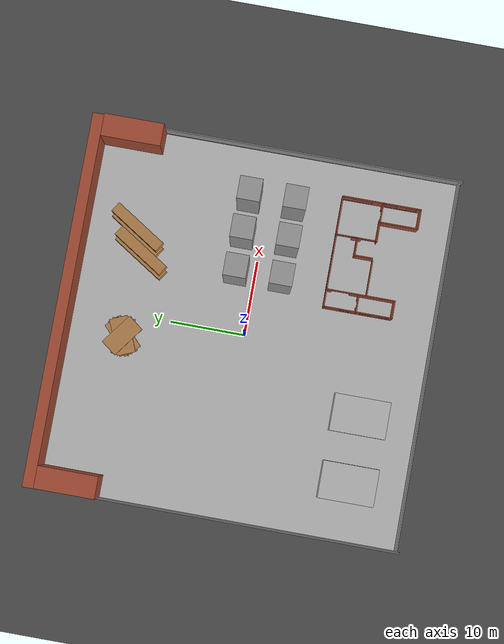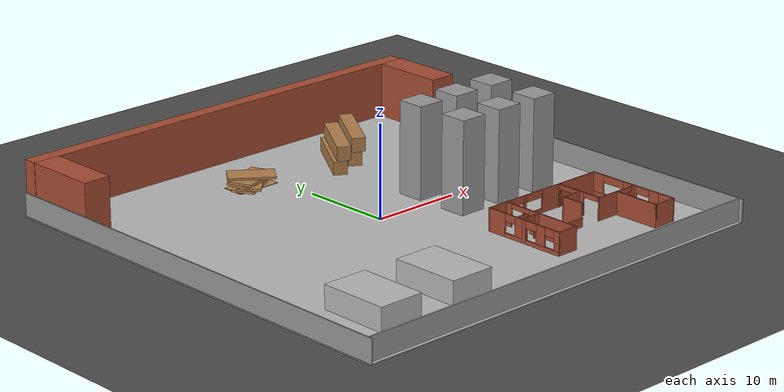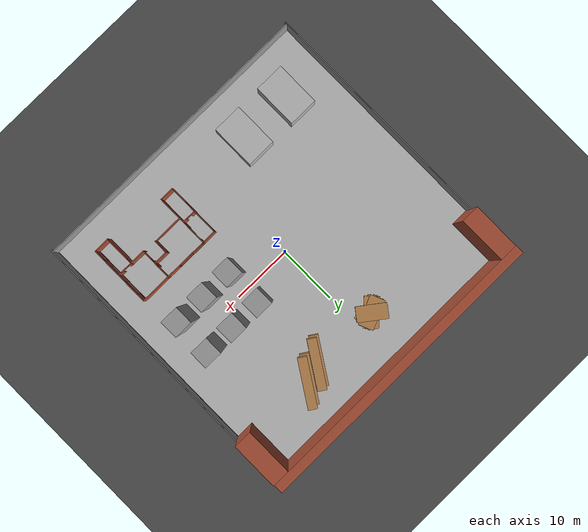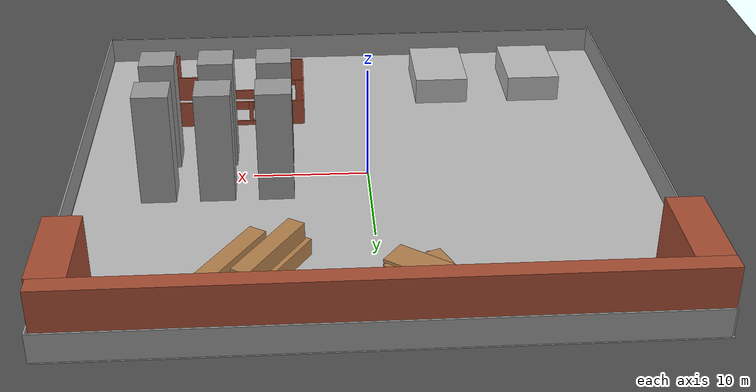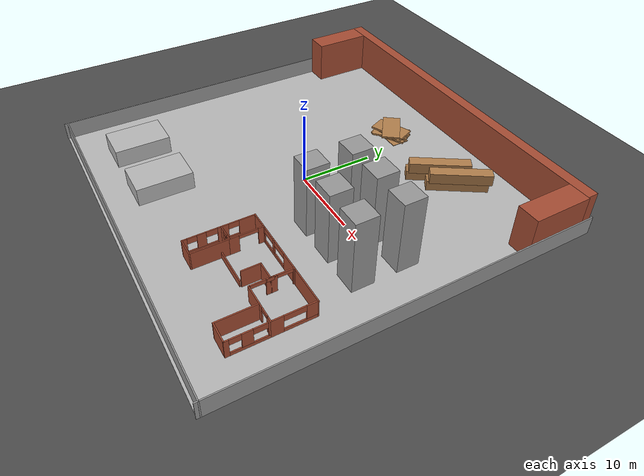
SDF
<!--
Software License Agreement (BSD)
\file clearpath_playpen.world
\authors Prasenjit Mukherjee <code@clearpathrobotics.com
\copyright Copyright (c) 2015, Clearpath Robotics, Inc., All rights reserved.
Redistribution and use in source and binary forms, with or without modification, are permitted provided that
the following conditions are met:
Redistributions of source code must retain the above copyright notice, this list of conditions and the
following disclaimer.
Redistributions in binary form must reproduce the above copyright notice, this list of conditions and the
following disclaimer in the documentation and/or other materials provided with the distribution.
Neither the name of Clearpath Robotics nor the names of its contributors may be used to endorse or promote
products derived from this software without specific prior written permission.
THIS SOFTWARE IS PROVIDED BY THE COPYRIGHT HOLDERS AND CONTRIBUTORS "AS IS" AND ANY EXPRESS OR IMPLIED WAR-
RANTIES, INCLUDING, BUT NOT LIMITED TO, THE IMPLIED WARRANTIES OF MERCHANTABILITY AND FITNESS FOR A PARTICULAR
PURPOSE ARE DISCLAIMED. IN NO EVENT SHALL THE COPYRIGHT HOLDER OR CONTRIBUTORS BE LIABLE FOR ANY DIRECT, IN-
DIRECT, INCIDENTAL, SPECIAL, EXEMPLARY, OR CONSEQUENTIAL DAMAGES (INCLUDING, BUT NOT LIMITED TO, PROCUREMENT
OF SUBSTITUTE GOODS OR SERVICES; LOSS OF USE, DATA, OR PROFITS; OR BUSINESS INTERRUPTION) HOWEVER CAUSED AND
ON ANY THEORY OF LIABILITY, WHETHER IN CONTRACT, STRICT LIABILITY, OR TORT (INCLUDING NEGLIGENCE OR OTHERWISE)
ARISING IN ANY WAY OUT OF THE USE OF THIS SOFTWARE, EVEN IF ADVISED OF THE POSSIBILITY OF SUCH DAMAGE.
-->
<sdf version="1.4">
 <world name="default">
  <light name="sun" type="directional">
   <pose>0 0 10 0 -0 0</pose>
   <diffuse>0.8 0.8 0.8 1</diffuse>
   <specular>0.2 0.2 0.2 1</specular>
   <attenuation>
    <range>1000</range>
    <constant>0.9</constant>
    <linear>0.01</linear>
    <quadratic>0.001</quadratic>
   </attenuation>
   <direction>-0.5 0.1 -0.9</direction>
  </light>
  <model name="ground_plane">
   <static>1</static>
   <link name="link">
    <collision name="collision">
     <geometry><plane><normal>0 0 1</normal><size>100 100</size></plane></geometry>
     <surface><friction><ode><mu>100</mu><mu2>50</mu2></ode></friction></surface>
    </collision>
    <visual name="visual">
     <cast_shadows>0</cast_shadows>
     <geometry><plane><normal>0 0 1</normal><size>100 100</size></plane></geometry>
     <material>
      <script>
       <uri>model://asphalt_plane/materials/scripts</uri>
       <uri>model://asphalt_plane/materials/textures</uri>
       <name>vrc/asphalt</name>
      </script>
     </material>
    </visual>
    <velocity_decay><linear>0</linear><angular>0</angular></velocity_decay>
   </link>
  </model>
  <physics type="ode">
   <max_step_size>0.01</max_step_size>
   <real_time_factor>1</real_time_factor>
   <real_time_update_rate>100</real_time_update_rate>
   <gravity>0 0 -9.8</gravity>
  </physics>
  <scene><ambient>0.4 0.4 0.4 1</ambient><background>0.7 0.7 0.7 1</background><shadows>1</shadows></scene>
  <model name="asphalt_plane">
   <static>1</static>
   <link name="link">
    <collision name="collision"><geometry><box><size>50 50 0.1</size></box></geometry></collision>
    <visual name="visual">
     <cast_shadows>0</cast_shadows>
     <geometry><box><size>50 50 0.1</size></box></geometry>
     <material>
      <script><uri>file://media/materials/scripts/gazebo.material</uri><name>Gazebo/Sand_Floor</name></script>
     </material>
    </visual>
    <velocity_decay><linear>0</linear><angular>0</angular></velocity_decay>
   </link>
   <pose>0.076733 -0.110379 0 0 -0 0</pose>
  </model>
  <model name="Wall_1">
   <include><static>true</static><uri>model://Wall</uri><pose>6.5 -30 0 0 0 0</pose></include>
  </model>
  <model name="Wall_2">
   <include><static>true</static><uri>model://Wall</uri><pose>6.5 19.5 0 0 0 0</pose></include>
  </model>
  <model name="Wall_3">
   <include><static>true</static><uri>model://Wall</uri><pose>30.5 6 0 0 0 1.57</pose></include>
  </model>
  <model name="Wall_4">
   <include><static>true</static><uri>model://Wall</uri><pose>-19.5 6 0 0 0 1.57</pose></include>
  </model>
  <model name="inside_house">
   <include><static>true</static><uri>model://construction_house</uri><pose>13 -15 0 0 0 0</pose></include>
  </model>
  <model name="Wood_1">
   <include><static>true</static><uri>model://Wood</uri><pose>-3 16 0 1.57 0 0</pose></include>
  </model>
  <model name="Wood_2">
   <include><static>true</static><uri>model://Wood</uri><pose>-3 16 0.25 1.57 0 0.5</pose></include>
  </model>
  <model name="Wood_3">
   <include><static>true</static><uri>model://Wood</uri><pose>-3 16 0.5 1.57 0 0.75</pose></include>
  </model>
  <model name="Wood_4">
   <include><static>true</static><uri>model://Wood</uri><pose>-3 16 0.75 1.57 0 0.2</pose></include>
  </model>
  <model name="Wood_5">
   <include><static>true</static><uri>model://Wood</uri><pose>-3 16 1 1.57 0 0.4</pose></include>
  </model>
  <model name="Wood_6">
   <include><static>true</static><uri>model://Wood</uri><pose>-3 16 1.25 1.57 0 2.5</pose></include>
  </model>
  <model name="Stone_1">
   <include><static>true</static><uri>model://Stone</uri><pose>-17 -17 1.277294 0 0 0</pose></include>
  </model>
  <model name="Stone_2">
   <include><static>true</static><uri>model://Stone</uri><pose>-8 -17 1.277294 0 0 0</pose></include>
  </model>
  <model name="long_wood_1">
   <include><static>true</static><uri>model://long_wood</uri><pose>8 15.5 0.75 0 0 1</pose></include>
  </model>
  <model name="long_wood_2">
   <include><static>true</static><uri>model://long_wood</uri><pose>11 16.5 0.75 0 0 1</pose></include>
  </model>
  <model name="long_wood_4">
   <include><static>true</static><uri>model://long_wood</uri><pose>8.5 15.5 2.25 0 0 1</pose></include>
  </model>
  <model name="long_wood_5">
   <include><static>true</static><uri>model://long_wood</uri><pose>11.5 16.5 2.25 0 0 1</pose></include>
  </model>
  <model name="storage_wall">
   <include><static>true</static><uri>model://storage_wall</uri><pose>0.12 23.95 3 0 0 0</pose></include>
  </model>
  <model name="storage_wall_2">
   <include><static>true</static><uri>model://storage_wall_2</uri><pose>-23.2049 19.2 3 0 0 1.57</pose></include>
  </model>
  <model name="storage_wall_3">
   <include><static>true</static><uri>model://storage_wall_2</uri><pose>23.6455 19.2 3 0 0 1.57</pose></include>
  </model>
  <model name="pillar_1">
   <include><static>true</static><uri>model://pillar</uri><pose>8 2.5 5 0 0 0</pose></include>
  </model>
  <model name="pillar_2">
   <include><static>true</static><uri>model://pillar</uri><pose>13 2.5 5 0 0 0</pose></include>
  </model>
  <model name="pillar_3">
   <include><static>true</static><uri>model://pillar</uri><pose>18 2.5 5 0 0 0</pose></include>
  </model>
  <model name="pillar_4">
   <include><static>true</static><uri>model://pillar</uri><pose>8 -3.5 5 0 0 0</pose></include>
  </model>
  <model name="pillar_5">
   <include><static>true</static><uri>model://pillar</uri><pose>13 -3.5 5 0 0 0</pose></include>
  </model>
  <model name="pillar_6">
   <include><static>true</static><uri>model://pillar</uri><pose>18 -3.5 5 0 0 0</pose></include>
  </model>
 </world>
</sdf>

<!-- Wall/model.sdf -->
<sdf version='1.6'>
  <model name='Wall'>
<link name='Wall_84'>
      <pose frame=''>-6.2 5.275 0 0 -0 3.14159</pose>
      <self_collide>0</self_collide>
      <kinematic>0</kinematic>
      <visual name='Wall_84_Visual'>
        <pose frame=''>0 0 1.25 0 -0 0</pose>
        <geometry>
          <box>
            <size>50 0.15 2.5</size>
          </box>
        </geometry>
        <material>
          <script>
              <uri>model://grey_wall/materials/scripts</uri>
            <uri>model://grey_wall/materials/textures</uri>
            <name>vrc/grey_wall</name>
          </script>
          <ambient>1 1 1 1</ambient>
          <diffuse>1 1 1 1</diffuse>
          <specular>0.2 0.2 0.2 1</specular>
          <emissive>0 0 0 1</emissive>
        </material>
        <cast_shadows>1</cast_shadows>
        <transparency>0</transparency>
      </visual>
      <collision name='Wall_84_Collision'>
        <laser_retro>0</laser_retro>
        <max_contacts>10</max_contacts>
        <pose frame=''>0 0 1.25 0 -0 0</pose>
        <geometry>
          <box>
            <size>50 0.15 2.5</size>
          </box>
        </geometry>
        <surface>
          <friction>
            <ode>
              <mu>1</mu>
              <mu2>1</mu2>
              <fdir1>0 0 0</fdir1>
              <slip1>0</slip1>
              <slip2>0</slip2>
            </ode>
            <torsional>
              <coefficient>1</coefficient>
              <patch_radius>0</patch_radius>
              <surface_radius>0</surface_radius>
              <use_patch_radius>1</use_patch_radius>
              <ode>
                <slip>0</slip>
              </ode>
            </torsional>
          </friction>
          <bounce>
            <restitution_coefficient>0</restitution_coefficient>
            <threshold>1e+06</threshold>
          </bounce>
          <contact>
            <collide_without_contact>0</collide_without_contact>
            <collide_without_contact_bitmask>1</collide_without_contact_bitmask>
            <collide_bitmask>1</collide_bitmask>
            <ode>
              <soft_cfm>0</soft_cfm>
              <soft_erp>0.2</soft_erp>
              <kp>1e+13</kp>
              <kd>1</kd>
              <max_vel>0.01</max_vel>
              <min_depth>0</min_depth>
            </ode>
            <bullet>
              <split_impulse>1</split_impulse>
              <split_impulse_penetration_threshold>-0.01</split_impulse_penetration_threshold>
              <soft_cfm>0</soft_cfm>
              <soft_erp>0.2</soft_erp>
              <kp>1e+13</kp>
              <kd>1</kd>
            </bullet>
          </contact>
        </surface>
      </collision>
    </link>
</model>
</sdf>

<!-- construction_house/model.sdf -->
<sdf version='1.6'>
  <model name='construction_house'>
    <link name='Wall_101'>
      <pose frame=''>-0.05 1.2 0 0 0 -1.5708</pose>
      <self_collide>0</self_collide>
      <kinematic>0</kinematic>
      <visual name='Wall_101_Visual'>
        <pose frame=''>0 0 1.25 0 -0 0</pose>
        <geometry>
          <box>
            <size>2.5 0.15 2.5</size>
          </box>
        </geometry>
        <material>
          <script>
            <uri>file://media/materials/scripts/gazebo.material</uri>
            <name>Gazebo/Bricks</name>
          </script>
          <ambient>1 1 1 1</ambient>
          <diffuse>1 1 1 1</diffuse>
          <specular>0.2 0.2 0.2 1</specular>
          <emissive>0 0 0 1</emissive>
        </material>
        <cast_shadows>1</cast_shadows>
        <transparency>0</transparency>
      </visual>
      <collision name='Wall_101_Collision'>
        <laser_retro>0</laser_retro>
        <max_contacts>10</max_contacts>
        <pose frame=''>0 0 1.25 0 -0 0</pose>
        <geometry>
          <box>
            <size>2.5 0.15 2.5</size>
          </box>
        </geometry>
        <surface>
          <friction>
            <ode>
              <mu>1</mu>
              <mu2>1</mu2>
              <fdir1>0 0 0</fdir1>
              <slip1>0</slip1>
              <slip2>0</slip2>
            </ode>
            <torsional>
              <coefficient>1</coefficient>
              <patch_radius>0</patch_radius>
              <surface_radius>0</surface_radius>
              <use_patch_radius>1</use_patch_radius>
              <ode>
                <slip>0</slip>
              </ode>
            </torsional>
          </friction>
          <bounce>
            <restitution_coefficient>0</restitution_coefficient>
            <threshold>1e+06</threshold>
          </bounce>
          <contact>
            <collide_without_contact>0</collide_without_contact>
            <collide_without_contact_bitmask>1</collide_without_contact_bitmask>
            <collide_bitmask>1</collide_bitmask>
            <ode>
              <soft_cfm>0</soft_cfm>
              <soft_erp>0.2</soft_erp>
              <kp>1e+13</kp>
              <kd>1</kd>
              <max_vel>0.01</max_vel>
              <min_depth>0</min_depth>
            </ode>
            <bullet>
              <split_impulse>1</split_impulse>
              <split_impulse_penetration_threshold>-0.01</split_impulse_penetration_threshold>
              <soft_cfm>0</soft_cfm>
              <soft_erp>0.2</soft_erp>
              <kp>1e+13</kp>
              <kd>1</kd>
            </bullet>
          </contact>
        </surface>
      </collision>
    </link>
    <link name='Wall_104'>
      <pose frame=''>2.3 3.1 0 0 -0 1.5708</pose>
      <self_collide>0</self_collide>
      <kinematic>0</kinematic>
      <visual name='Wall_104_Visual_1'>
        <pose frame=''>2.11625 0 1.25 0 -0 0</pose>
        <geometry>
          <box>
            <size>0.267504 0.15 2.5</size>
          </box>
        </geometry>
        <material>
          <script>
            <uri>file://media/materials/scripts/gazebo.material</uri>
            <name>Gazebo/Bricks</name>
          </script>
          <ambient>1 1 1 1</ambient>
          <diffuse>1 1 1 1</diffuse>
          <specular>0.2 0.2 0.2 1</specular>
          <emissive>0 0 0 1</emissive>
        </material>
        <cast_shadows>1</cast_shadows>
        <transparency>0</transparency>
      </visual>
      <visual name='Wall_104_Visual_2'>
        <pose frame=''>0.5325 0 2.25 0 -0 0</pose>
        <geometry>
          <box>
            <size>2.9 0.15 0.5</size>
          </box>
        </geometry>
        <material>
          <script>
            <uri>file://media/materials/scripts/gazebo.material</uri>
            <name>Gazebo/Bricks</name>
          </script>
          <ambient>1 1 1 1</ambient>
          <diffuse>1 1 1 1</diffuse>
          <specular>0.2 0.2 0.2 1</specular>
          <emissive>0 0 0 1</emissive>
        </material>
        <cast_shadows>1</cast_shadows>
        <transparency>0</transparency>
      </visual>
      <visual name='Wall_104_Visual_0'>
        <pose frame=''>-0.583752 0 1.25 0 -0 0</pose>
        <geometry>
          <box>
            <size>1.3325 0.15 2.5</size>
          </box>
        </geometry>
        <material>
          <script>
            <uri>file://media/materials/scripts/gazebo.material</uri>
            <name>Gazebo/Bricks</name>
          </script>
          <ambient>1 1 1 1</ambient>
          <diffuse>1 1 1 1</diffuse>
          <specular>0.2 0.2 0.2 1</specular>
          <emissive>0 0 0 1</emissive>
        </material>
        <cast_shadows>1</cast_shadows>
        <transparency>0</transparency>
      </visual>
      <collision name='Wall_104_Collision_1'>
        <laser_retro>0</laser_retro>
        <max_contacts>10</max_contacts>
        <pose frame=''>2.11625 0 1.25 0 -0 0</pose>
        <geometry>
          <box>
            <size>0.267504 0.15 2.5</size>
          </box>
        </geometry>
        <surface>
          <friction>
            <ode>
              <mu>1</mu>
              <mu2>1</mu2>
              <fdir1>0 0 0</fdir1>
              <slip1>0</slip1>
              <slip2>0</slip2>
            </ode>
            <torsional>
              <coefficient>1</coefficient>
              <patch_radius>0</patch_radius>
              <surface_radius>0</surface_radius>
              <use_patch_radius>1</use_patch_radius>
              <ode>
                <slip>0</slip>
              </ode>
            </torsional>
          </friction>
          <bounce>
            <restitution_coefficient>0</restitution_coefficient>
            <threshold>1e+06</threshold>
          </bounce>
          <contact>
            <collide_without_contact>0</collide_without_contact>
            <collide_without_contact_bitmask>1</collide_without_contact_bitmask>
            <collide_bitmask>1</collide_bitmask>
            <ode>
              <soft_cfm>0</soft_cfm>
              <soft_erp>0.2</soft_erp>
              <kp>1e+13</kp>
              <kd>1</kd>
              <max_vel>0.01</max_vel>
              <min_depth>0</min_depth>
            </ode>
            <bullet>
              <split_impulse>1</split_impulse>
              <split_impulse_penetration_threshold>-0.01</split_impulse_penetration_threshold>
              <soft_cfm>0</soft_cfm>
              <soft_erp>0.2</soft_erp>
              <kp>1e+13</kp>
              <kd>1</kd>
            </bullet>
          </contact>
        </surface>
      </collision>
      <collision name='Wall_104_Collision_2'>
        <laser_retro>0</laser_retro>
        <max_contacts>10</max_contacts>
        <pose frame=''>0.5325 0 2.25 0 -0 0</pose>
        <geometry>
          <box>
            <size>2.9 0.15 0.5</size>
          </box>
        </geometry>
        <surface>
          <friction>
            <ode>
              <mu>1</mu>
              <mu2>1</mu2>
              <fdir1>0 0 0</fdir1>
              <slip1>0</slip1>
              <slip2>0</slip2>
            </ode>
            <torsional>
              <coefficient>1</coefficient>
              <patch_radius>0</patch_radius>
              <surface_radius>0</surface_radius>
              <use_patch_radius>1</use_patch_radius>
              <ode>
                <slip>0</slip>
              </ode>
            </torsional>
          </friction>
          <bounce>
            <restitution_coefficient>0</restitution_coefficient>
            <threshold>1e+06</threshold>
          </bounce>
          <contact>
            <collide_without_contact>0</collide_without_contact>
            <collide_without_contact_bitmask>1</collide_without_contact_bitmask>
            <collide_bitmask>1</collide_bitmask>
            <ode>
              <soft_cfm>0</soft_cfm>
              <soft_erp>0.2</soft_erp>
              <kp>1e+13</kp>
              <kd>1</kd>
              <max_vel>0.01</max_vel>
              <min_depth>0</min_depth>
            </ode>
            <bullet>
              <split_impulse>1</split_impulse>
              <split_impulse_penetration_threshold>-0.01</split_impulse_penetration_threshold>
              <soft_cfm>0</soft_cfm>
              <soft_erp>0.2</soft_erp>
              <kp>1e+13</kp>
              <kd>1</kd>
            </bullet>
          </contact>
        </surface>
      </collision>
      <collision name='Wall_104_Collision_0'>
        <laser_retro>0</laser_retro>
        <max_contacts>10</max_contacts>
        <pose frame=''>-0.583752 0 1.25 0 -0 0</pose>
        <geometry>
          <box>
            <size>1.3325 0.15 2.5</size>
          </box>
        </geometry>
        <surface>
          <friction>
            <ode>
              <mu>1</mu>
              <mu2>1</mu2>
              <fdir1>0 0 0</fdir1>
              <slip1>0</slip1>
              <slip2>0</slip2>
            </ode>
            <torsional>
              <coefficient>1</coefficient>
              <patch_radius>0</patch_radius>
              <surface_radius>0</surface_radius>
              <use_patch_radius>1</use_patch_radius>
              <ode>
                <slip>0</slip>
              </ode>
            </torsional>
          </friction>
          <bounce>
            <restitution_coefficient>0</restitution_coefficient>
            <threshold>1e+06</threshold>
          </bounce>
          <contact>
            <collide_without_contact>0</collide_without_contact>
            <collide_without_contact_bitmask>1</collide_without_contact_bitmask>
            <collide_bitmask>1</collide_bitmask>
            <ode>
              <soft_cfm>0</soft_cfm>
              <soft_erp>0.2</soft_erp>
              <kp>1e+13</kp>
              <kd>1</kd>
              <max_vel>0.01</max_vel>
              <min_depth>0</min_depth>
            </ode>
            <bullet>
              <split_impulse>1</split_impulse>
              <split_impulse_penetration_threshold>-0.01</split_impulse_penetration_threshold>
              <soft_cfm>0</soft_cfm>
              <soft_erp>0.2</soft_erp>
              <kp>1e+13</kp>
              <kd>1</kd>
            </bullet>
          </contact>
        </surface>
      </collision>
    </link>
    <link name='Wall_106'>
      <pose frame=''>6.2 -0.175 0 0 -0 0</pose>
      <self_collide>0</self_collide>
      <kinematic>0</kinematic>
      <visual name='Wall_106_Visual_1'>
        <pose frame=''>0.922235 0 1.25 0 -0 0</pose>
        <geometry>
          <box>
            <size>0.905529 0.15 2.5</size>
          </box>
        </geometry>
        <material>
          <script>
            <uri>file://media/materials/scripts/gazebo.material</uri>
            <name>Gazebo/Bricks</name>
          </script>
          <ambient>1 1 1 1</ambient>
          <diffuse>1 1 1 1</diffuse>
          <specular>0.2 0.2 0.2 1</specular>
          <emissive>0 0 0 1</emissive>
        </material>
        <cast_shadows>1</cast_shadows>
        <transparency>0</transparency>
      </visual>
      <visual name='Wall_106_Visual_2'>
        <pose frame=''>0.019471 0 2.25 0 -0 0</pose>
        <geometry>
          <box>
            <size>1.5 0.15 0.5</size>
          </box>
        </geometry>
        <material>
          <script>
            <uri>file://media/materials/scripts/gazebo.material</uri>
            <name>Gazebo/Bricks</name>
          </script>
          <ambient>1 1 1 1</ambient>
          <diffuse>1 1 1 1</diffuse>
          <specular>0.2 0.2 0.2 1</specular>
          <emissive>0 0 0 1</emissive>
        </material>
        <cast_shadows>1</cast_shadows>
        <transparency>0</transparency>
      </visual>
      <visual name='Wall_106_Visual_0'>
        <pose frame=''>-1 0 1.25 0 -0 0</pose>
        <geometry>
          <box>
            <size>0.5 0.15 2.5</size>
          </box>
        </geometry>
        <material>
          <script>
            <uri>file://media/materials/scripts/gazebo.material</uri>
            <name>Gazebo/Bricks</name>
          </script>
          <ambient>1 1 1 1</ambient>
          <diffuse>1 1 1 1</diffuse>
          <specular>0.2 0.2 0.2 1</specular>
          <emissive>0 0 0 1</emissive>
        </material>
        <cast_shadows>1</cast_shadows>
        <transparency>0</transparency>
      </visual>
      <collision name='Wall_106_Collision_1'>
        <laser_retro>0</laser_retro>
        <max_contacts>10</max_contacts>
        <pose frame=''>0.922235 0 1.25 0 -0 0</pose>
        <geometry>
          <box>
            <size>0.905529 0.15 2.5</size>
          </box>
        </geometry>
        <surface>
          <friction>
            <ode>
              <mu>1</mu>
              <mu2>1</mu2>
              <fdir1>0 0 0</fdir1>
              <slip1>0</slip1>
              <slip2>0</slip2>
            </ode>
            <torsional>
              <coefficient>1</coefficient>
              <patch_radius>0</patch_radius>
              <surface_radius>0</surface_radius>
              <use_patch_radius>1</use_patch_radius>
              <ode>
                <slip>0</slip>
              </ode>
            </torsional>
          </friction>
          <bounce>
            <restitution_coefficient>0</restitution_coefficient>
            <threshold>1e+06</threshold>
          </bounce>
          <contact>
            <collide_without_contact>0</collide_without_contact>
            <collide_without_contact_bitmask>1</collide_without_contact_bitmask>
            <collide_bitmask>1</collide_bitmask>
            <ode>
              <soft_cfm>0</soft_cfm>
              <soft_erp>0.2</soft_erp>
              <kp>1e+13</kp>
              <kd>1</kd>
              <max_vel>0.01</max_vel>
              <min_depth>0</min_depth>
            </ode>
            <bullet>
              <split_impulse>1</split_impulse>
              <split_impulse_penetration_threshold>-0.01</split_impulse_penetration_threshold>
              <soft_cfm>0</soft_cfm>
              <soft_erp>0.2</soft_erp>
              <kp>1e+13</kp>
              <kd>1</kd>
            </bullet>
          </contact>
        </surface>
      </collision>
      <collision name='Wall_106_Collision_0'>
        <laser_retro>0</laser_retro>
        <max_contacts>10</max_contacts>
        <pose frame=''>-1 0 1.25 0 -0 0</pose>
        <geometry>
          <box>
            <size>0.5 0.15 2.5</size>
          </box>
        </geometry>
        <surface>
          <friction>
            <ode>
              <mu>1</mu>
              <mu2>1</mu2>
              <fdir1>0 0 0</fdir1>
              <slip1>0</slip1>
              <slip2>0</slip2>
            </ode>
            <torsional>
              <coefficient>1</coefficient>
              <patch_radius>0</patch_radius>
              <surface_radius>0</surface_radius>
              <use_patch_radius>1</use_patch_radius>
              <ode>
                <slip>0</slip>
              </ode>
            </torsional>
          </friction>
          <bounce>
            <restitution_coefficient>0</restitution_coefficient>
            <threshold>1e+06</threshold>
          </bounce>
          <contact>
            <collide_without_contact>0</collide_without_contact>
            <collide_without_contact_bitmask>1</collide_without_contact_bitmask>
            <collide_bitmask>1</collide_bitmask>
            <ode>
              <soft_cfm>0</soft_cfm>
              <soft_erp>0.2</soft_erp>
              <kp>1e+13</kp>
              <kd>1</kd>
              <max_vel>0.01</max_vel>
              <min_depth>0</min_depth>
            </ode>
            <bullet>
              <split_impulse>1</split_impulse>
              <split_impulse_penetration_threshold>-0.01</split_impulse_penetration_threshold>
              <soft_cfm>0</soft_cfm>
              <soft_erp>0.2</soft_erp>
              <kp>1e+13</kp>
              <kd>1</kd>
            </bullet>
          </contact>
        </surface>
      </collision>
      <collision name='Wall_106_Collision_2'>
        <laser_retro>0</laser_retro>
        <max_contacts>10</max_contacts>
        <pose frame=''>0.019471 0 2.25 0 -0 0</pose>
        <geometry>
          <box>
            <size>1.5 0.15 0.5</size>
          </box>
        </geometry>
        <surface>
          <friction>
            <ode>
              <mu>1</mu>
              <mu2>1</mu2>
              <fdir1>0 0 0</fdir1>
              <slip1>0</slip1>
              <slip2>0</slip2>
            </ode>
            <torsional>
              <coefficient>1</coefficient>
              <patch_radius>0</patch_radius>
              <surface_radius>0</surface_radius>
              <use_patch_radius>1</use_patch_radius>
              <ode>
                <slip>0</slip>
              </ode>
            </torsional>
          </friction>
          <bounce>
            <restitution_coefficient>0</restitution_coefficient>
            <threshold>1e+06</threshold>
          </bounce>
          <contact>
            <collide_without_contact>0</collide_without_contact>
            <collide_without_contact_bitmask>1</collide_without_contact_bitmask>
            <collide_bitmask>1</collide_bitmask>
            <ode>
              <soft_cfm>0</soft_cfm>
              <soft_erp>0.2</soft_erp>
              <kp>1e+13</kp>
              <kd>1</kd>
              <max_vel>0.01</max_vel>
              <min_depth>0</min_depth>
            </ode>
            <bullet>
              <split_impulse>1</split_impulse>
              <split_impulse_penetration_threshold>-0.01</split_impulse_penetration_threshold>
              <soft_cfm>0</soft_cfm>
              <soft_erp>0.2</soft_erp>
              <kp>1e+13</kp>
              <kd>1</kd>
            </bullet>
          </contact>
        </surface>
      </collision>
    </link>
    <link name='Wall_108'>
      <pose frame=''>-1.6 -0.17488 0 0 -0 0</pose>
      <self_collide>0</self_collide>
      <kinematic>0</kinematic>
      <visual name='Wall_108_Visual_0'>
        <pose frame=''>-1 0 0.5 0 -0 0</pose>
        <geometry>
          <box>
            <size>5 0.15 1</size>
          </box>
        </geometry>
        <material>
          <script>
            <uri>file://media/materials/scripts/gazebo.material</uri>
            <name>Gazebo/Bricks</name>
          </script>
          <ambient>1 1 1 1</ambient>
          <diffuse>1 1 1 1</diffuse>
          <specular>0.2 0.2 0.2 1</specular>
          <emissive>0 0 0 1</emissive>Here is my progress so far:
1. Extended the gazebo world to a larger construction site, added and modified some objects in the gazebo world.
2. Configured rviz file for the SLAM application.
3. Created a map using gmapping and teleop
4. Used the map created by SLAM to do navigation.
5. Created a launch file to open gazebo world, rviz and gmapping.

Doing:
1. Modify the gazebo world and add more objects.
2. Try to use joystick to control the robot in gazebo
        </material>
        <cast_shadows>1</cast_shadows>
        <transparency>0</transparency>
      </visual>

      <collision name='Wall_108_Collision_0'>
        <laser_retro>0</laser_retro>
        <max_contacts>10</max_contacts>
        <pose frame=''>-0.856324 0 0.5 0 -0 0</pose>
        <geometry>
          <box>
            <size>5 0.15 1</size>
          </box>
        </geometry>
        <surface>
          <friction>
            <ode>
              <mu>1</mu>
              <mu2>1</mu2>
              <fdir1>0 0 0</fdir1>
              <slip1>0</slip1>
              <slip2>0</slip2>
            </ode>
            <torsional>
              <coefficient>1</coefficient>
              <patch_radius>0</patch_radius>
              <surface_radius>0</surface_radius>
              <use_patch_radius>1</use_patch_radius>
              <ode>
                <slip>0</slip>
              </ode>
            </torsional>
          </friction>
          <bounce>
            <restitution_coefficient>0</restitution_coefficient>
            <threshold>1e+06</threshold>
          </bounce>
          <contact>
            <collide_without_contact>0</collide_without_contact>
            <collide_without_contact_bitmask>1</collide_without_contact_bitmask>
            <collide_bitmask>1</collide_bitmask>
            <ode>
              <soft_cfm>0</soft_cfm>
              <soft_erp>0.2</soft_erp>
              <kp>1e+13</kp>
              <kd>1</kd>
              <max_vel>0.01</max_vel>
              <min_depth>0</min_depth>
            </ode>
            <bullet>
              <split_impulse>1</split_impulse>
              <split_impulse_penetration_threshold>-0.01</split_impulse_penetration_threshold>
              <soft_cfm>0</soft_cfm>
              <soft_erp>0.2</soft_erp>
              <kp>1e+13</kp>
              <kd>1</kd>
            </bullet>
          </contact>
        </surface>
      </collision>
    </link>
    <link name='Wall_81'>
      <pose frame=''>5.07752 5.2688 0 0 -0 3.14159</pose>
      <self_collide>0</self_collide>
      <kinematic>0</kinematic>
      <visual name='Wall_81_Visual'>
        <pose frame=''>0 0 1.25 0 -0 0</pose>
        <geometry>
          <box>
            <size>5 0.15 2.5</size>
          </box>
        </geometry>
        <material>
          <script>
            <uri>file://media/materials/scripts/gazebo.material</uri>
            <name>Gazebo/Bricks</name>
          </script>
          <ambient>1 1 1 1</ambient>
          <diffuse>1 1 1 1</diffuse>
          <specular>0.2 0.2 0.2 1</specular>
          <emissive>0 0 0 1</emissive>
        </material>
        <cast_shadows>1</cast_shadows>
        <transparency>0</transparency>
      </visual>
      <collision name='Wall_81_Collision'>
        <laser_retro>0</laser_retro>
        <max_contacts>10</max_contacts>
        <pose frame=''>0 0 1.25 0 -0 0</pose>
        <geometry>
          <box>
            <size>5 0.15 2.5</size>
          </box>
        </geometry>
        <surface>
          <friction>
            <ode>
              <mu>1</mu>
              <mu2>1</mu2>
              <fdir1>0 0 0</fdir1>
              <slip1>0</slip1>
              <slip2>0</slip2>
            </ode>
            <torsional>
              <coefficient>1</coefficient>
              <patch_radius>0</patch_radius>
              <surface_radius>0</surface_radius>
              <use_patch_radius>1</use_patch_radius>
              <ode>
                <slip>0</slip>
              </ode>
            </torsional>
          </friction>
          <bounce>
            <restitution_coefficient>0</restitution_coefficient>
            <threshold>1e+06</threshold>
          </bounce>
          <contact>
            <collide_without_contact>0</collide_without_contact>
            <collide_without_contact_bitmask>1</collide_without_contact_bitmask>
            <collide_bitmask>1</collide_bitmask>
            <ode>
              <soft_cfm>0</soft_cfm>
              <soft_erp>0.2</soft_erp>
              <kp>1e+13</kp>
              <kd>1</kd>
              <max_vel>0.01</max_vel>
              <min_depth>0</min_depth>
            </ode>
            <bullet>
              <split_impulse>1</split_impulse>
              <split_impulse_penetration_threshold>-0.01</split_impulse_penetration_threshold>
              <soft_cfm>0</soft_cfm>
              <soft_erp>0.2</soft_erp>
              <kp>1e+13</kp>
              <kd>1</kd>
            </bullet>
          </contact>
        </surface>
      </collision>
    </link>
    <link name='Wall_82'>
      <pose frame=''>1.25 5.26876 0 0 -0 3.14159</pose>
      <self_collide>0</self_collide>
      <kinematic>0</kinematic>
      <visual name='Wall_82_Visual'>
        <pose frame=''>0 0 1.25 0 -0 0</pose>
        <geometry>
          <box>
            <size>2.75 0.15 2.5</size>
          </box>
        </geometry>
        <material>
          <script>
            <uri>file://media/materials/scripts/gazebo.material</uri>
            <name>Gazebo/Bricks</name>
          </script>
          <ambient>1 1 1 1</ambient>
          <diffuse>1 1 1 1</diffuse>
          <specular>0.2 0.2 0.2 1</specular>
          <emissive>0 0 0 1</emissive>
        </material>
        <cast_shadows>1</cast_shadows>
        <transparency>0</transparency>
      </visual>
      <collision name='Wall_82_Collision'>
        <laser_retro>0</laser_retro>
        <max_contacts>10</max_contacts>
        <pose frame=''>0 0 1.25 0 -0 0</pose>
        <geometry>
          <box>
            <size>2.75 0.15 2.5</size>
          </box>
        </geometry>
        <surface>
          <friction>
            <ode>
              <mu>1</mu>
              <mu2>1</mu2>
              <fdir1>0 0 0</fdir1>
              <slip1>0</slip1>
              <slip2>0</slip2>
            </ode>
            <torsional>
              <coefficient>1</coefficient>
              <patch_radius>0</patch_radius>
              <surface_radius>0</surface_radius>
              <use_patch_radius>1</use_patch_radius>
              <ode>
                <slip>0</slip>
              </ode>
            </torsional>
          </friction>
          <bounce>
            <restitution_coefficient>0</restitution_coefficient>
            <threshold>1e+06</threshold>
          </bounce>
          <contact>
            <collide_without_contact>0</collide_without_contact>
            <collide_without_contact_bitmask>1</collide_without_contact_bitmask>
            <collide_bitmask>1</collide_bitmask>
            <ode>
              <soft_cfm>0</soft_cfm>
              <soft_erp>0.2</soft_erp>
              <kp>1e+13</kp>
              <kd>1</kd>
              <max_vel>0.01</max_vel>
              <min_depth>0</min_depth>
            </ode>
            <bullet>
              <split_impulse>1</split_impulse>
              <split_impulse_penetration_threshold>-0.01</split_impulse_penetration_threshold>
              <soft_cfm>0</soft_cfm>
              <soft_erp>0.2</soft_erp>
              <kp>1e+13</kp>
              <kd>1</kd>
            </bullet>
          </contact>
        </surface>
      </collision>
    </link>
    <link name='Wall_83'>
      <pose frame=''>-2.475 5.275 0 0 -0 3.14159</pose>
      <self_collide>0</self_collide>
      <kinematic>0</kinematic>
      <visual name='Wall_83_Visual_2'>
        <pose frame=''>0.110246 0 1.5 0 -0 0</pose>
        <geometry>
          <box>
            <size>0.37052 0.15 2</size>
          </box>
        </geometry>
        <material>
          <script>
            <uri>file://media/materials/scripts/gazebo.material</uri>
            <name>Gazebo/Bricks</name>
          </script>
          <ambient>1 1 1 1</ambient>
          <diffuse>1 1 1 1</diffuse>
          <specular>0.2 0.2 0.2 1</specular>
          <emissive>0 0 0 1</emissive>
        </material>
        <cast_shadows>1</cast_shadows>
        <transparency>0</transparency>
      </visual>
      <visual name='Wall_83_Visual_6'>
        <pose frame=''>1.39775 0 2.1 0 -0 0</pose>
        <geometry>
          <box>
            <size>2.20449 0.15 0.8</size>
          </box>
        </geometry>
        <material>
          <script>
            <uri>file://media/materials/scripts/gazebo.material</uri>
            <name>Gazebo/Bricks</name>
          </script>
          <ambient>1 1 1 1</ambient>
          <diffuse>1 1 1 1</diffuse>
          <specular>0.2 0.2 0.2 1</specular>
          <emissive>0 0 0 1</emissive>
        </material>
        <cast_shadows>1</cast_shadows>
        <transparency>0</transparency>
      </visual>
      <visual name='Wall_83_Visual_3'>
        <pose frame=''>0.110246 0 1.5 0 -0 0</pose>
        <geometry>
          <box>
            <size>0.37052 0.15 2</size>
          </box>
        </geometry>
        <material>
          <script>
            <uri>file://media/materials/scripts/gazebo.material</uri>
            <name>Gazebo/Bricks</name>
          </script>
          <ambient>1 1 1 1</ambient>
          <diffuse>1 1 1 1</diffuse>
          <specular>0.2 0.2 0.2 1</specular>
          <emissive>0 0 0 1</emissive>
        </material>
        <cast_shadows>1</cast_shadows>
        <transparency>0</transparency>
      </visual>
      <visual name='Wall_83_Visual_1'>
        <pose frame=''>0.080993 0 0.25 0 -0 0</pose>
        <geometry>
          <box>
            <size>4.83801 0.15 0.5</size>
          </box>
        </geometry>
        <material>
          <script>
            <uri>file://media/materials/scripts/gazebo.material</uri>
            <name>Gazebo/Bricks</name>
          </script>
          <ambient>1 1 1 1</ambient>
          <diffuse>1 1 1 1</diffuse>
          <specular>0.2 0.2 0.2 1</specular>
          <emissive>0 0 0 1</emissive>
        </material>
        <cast_shadows>1</cast_shadows>
        <transparency>0</transparency>
      </visual>
      <visual name='Wall_83_Visual_4'>
        <pose frame=''>-1.20651 0 2.1 0 -0 0</pose>
        <geometry>
          <box>
            <size>2.263 0.15 0.8</size>
          </box>
        </geometry>
        <material>
          <script>
            <uri>file://media/materials/scripts/gazebo.material</uri>
            <name>Gazebo/Bricks</name>
          </script>
          <ambient>1 1 1 1</ambient>
          <diffuse>1 1 1 1</diffuse>
          <specular>0.2 0.2 0.2 1</specular>
          <emissive>0 0 0 1</emissive>
        </material>
        <cast_shadows>1</cast_shadows>
        <transparency>0</transparency>
      </visual>
      <visual name='Wall_83_Visual_5'>
        <pose frame=''>1.39775 0 2.1 0 -0 0</pose>
        <geometry>
          <box>
            <size>2.20449 0.15 0.8</size>
          </box>
        </geometry>
        <material>
          <script>
            <uri>file://media/materials/scripts/gazebo.material</uri>
            <name>Gazebo/Bricks</name>
          </script>
          <ambient>1 1 1 1</ambient>
          <diffuse>1 1 1 1</diffuse>
          <specular>0.2 0.2 0.2 1</specular>
          <emissive>0 0 0 1</emissive>
        </material>
        <cast_shadows>1</cast_shadows>
        <transparency>0</transparency>
      </visual>
      <visual name='Wall_83_Visual_0'>
        <pose frame=''>-2.41901 0 1.25 0 -0 0</pose>
        <geometry>
          <box>
            <size>0.161986 0.15 2.5</size>
          </box>
        </geometry>
        <material>
          <script>
            <uri>file://media/materials/scripts/gazebo.material</uri>
            <name>Gazebo/Bricks</name>
          </script>
          <ambient>1 1 1 1</ambient>
          <diffuse>1 1 1 1</diffuse>
          <specular>0.2 0.2 0.2 1</specular>
          <emissive>0 0 0 1</emissive>
        </material>
        <cast_shadows>1</cast_shadows>
        <transparency>0</transparency>
      </visual>
      <collision name='Wall_83_Collision_4'>
        <laser_retro>0</laser_retro>
        <max_contacts>10</max_contacts>
        <pose frame=''>-1.20651 0 2.1 0 -0 0</pose>
        <geometry>
          <box>
            <size>2.263 0.15 0.8</size>
          </box>
        </geometry>
        <surface>
          <friction>
            <ode>
              <mu>1</mu>
              <mu2>1</mu2>
              <fdir1>0 0 0</fdir1>
              <slip1>0</slip1>
              <slip2>0</slip2>
            </ode>
            <torsional>
              <coefficient>1</coefficient>
              <patch_radius>0</patch_radius>
              <surface_radius>0</surface_radius>
              <use_patch_radius>1</use_patch_radius>
              <ode>
                <slip>0</slip>
              </ode>
            </torsional>
          </friction>
          <bounce>
            <restitution_coefficient>0</restitution_coefficient>
            <threshold>1e+06</threshold>
          </bounce>
          <contact>
            <collide_without_contact>0</collide_without_contact>
            <collide_without_contact_bitmask>1</collide_without_contact_bitmask>
            <collide_bitmask>1</collide_bitmask>
            <ode>
              <soft_cfm>0</soft_cfm>
              <soft_erp>0.2</soft_erp>
              <kp>1e+13</kp>
              <kd>1</kd>
              <max_vel>0.01</max_vel>
              <min_depth>0</min_depth>
            </ode>
            <bullet>
              <split_impulse>1</split_impulse>
              <split_impulse_penetration_threshold>-0.01</split_impulse_penetration_threshold>
              <soft_cfm>0</soft_cfm>
              <soft_erp>0.2</soft_erp>
              <kp>1e+13</kp>
              <kd>1</kd>
            </bullet>
          </contact>
        </surface>
      </collision>
      <collision name='Wall_83_Collision_2'>
        <laser_retro>0</laser_retro>
        <max_contacts>10</max_contacts>
        <pose frame=''>0.110246 0 1.5 0 -0 0</pose>
        <geometry>
          <box>
            <size>0.37052 0.15 2</size>
          </box>
        </geometry>
        <surface>
          <friction>
            <ode>
              <mu>1</mu>
              <mu2>1</mu2>
              <fdir1>0 0 0</fdir1>
              <slip1>0</slip1>
              <slip2>0</slip2>
            </ode>
            <torsional>
              <coefficient>1</coefficient>
              <patch_radius>0</patch_radius>
              <surface_radius>0</surface_radius>
              <use_patch_radius>1</use_patch_radius>
              <ode>
                <slip>0</slip>
              </ode>
            </torsional>
          </friction>
          <bounce>
            <restitution_coefficient>0</restitution_coefficient>
            <threshold>1e+06</threshold>
          </bounce>
          <contact>
            <collide_without_contact>0</collide_without_contact>
            <collide_without_contact_bitmask>1</collide_without_contact_bitmask>
            <collide_bitmask>1</collide_bitmask>
            <ode>
              <soft_cfm>0</soft_cfm>
              <soft_erp>0.2</soft_erp>
              <kp>1e+13</kp>
              <kd>1</kd>
              <max_vel>0.01</max_vel>
              <min_depth>0</min_depth>
            </ode>
            <bullet>
              <split_impulse>1</split_impulse>
              <split_impulse_penetration_threshold>-0.01</split_impulse_penetration_threshold>
              <soft_cfm>0</soft_cfm>
              <soft_erp>0.2</soft_erp>
              <kp>1e+13</kp>
              <kd>1</kd>
            </bullet>
          </contact>
        </surface>
      </collision>
      <collision name='Wall_83_Collision_6'>
        <laser_retro>0</laser_retro>
        <max_contacts>10</max_contacts>
        <pose frame=''>1.39775 0 2.1 0 -0 0</pose>
        <geometry>
          <box>
            <size>2.20449 0.15 0.8</size>
          </box>
        </geometry>
        <surface>
          <friction>
            <ode>
              <mu>1</mu>
              <mu2>1</mu2>
              <fdir1>0 0 0</fdir1>
              <slip1>0</slip1>
              <slip2>0</slip2>
            </ode>
            <torsional>
              <coefficient>1</coefficient>
              <patch_radius>0</patch_radius>
              <surface_radius>0</surface_radius>
              <use_patch_radius>1</use_patch_radius>
              <ode>
                <slip>0</slip>
              </ode>
            </torsional>
          </friction>
          <bounce>
            <restitution_coefficient>0</restitution_coefficient>
            <threshold>1e+06</threshold>
          </bounce>
          <contact>
            <collide_without_contact>0</collide_without_contact>
            <collide_without_contact_bitmask>1</collide_without_contact_bitmask>
            <collide_bitmask>1</collide_bitmask>
            <ode>
              <soft_cfm>0</soft_cfm>
              <soft_erp>0.2</soft_erp>
              <kp>1e+13</kp>
              <kd>1</kd>
              <max_vel>0.01</max_vel>
              <min_depth>0</min_depth>
            </ode>
            <bullet>
              <split_impulse>1</split_impulse>
              <split_impulse_penetration_threshold>-0.01</split_impulse_penetration_threshold>
              <soft_cfm>0</soft_cfm>
              <soft_erp>0.2</soft_erp>
              <kp>1e+13</kp>
              <kd>1</kd>
            </bullet>
          </contact>
        </surface>
      </collision>
      <collision name='Wall_83_Collision_0'>
        <laser_retro>0</laser_retro>
        <max_contacts>10</max_contacts>
        <pose frame=''>-2.41901 0 1.25 0 -0 0</pose>
        <geometry>
          <box>
            <size>0.161986 0.15 2.5</size>
          </box>
        </geometry>
        <surface>
          <friction>
            <ode>
              <mu>1</mu>
              <mu2>1</mu2>
              <fdir1>0 0 0</fdir1>
              <slip1>0</slip1>
              <slip2>0</slip2>
            </ode>
            <torsional>
              <coefficient>1</coefficient>
              <patch_radius>0</patch_radius>
              <surface_radius>0</surface_radius>
              <use_patch_radius>1</use_patch_radius>
              <ode>
                <slip>0</slip>
              </ode>
            </torsional>
          </friction>
          <bounce>
            <restitution_coefficient>0</restitution_coefficient>
            <threshold>1e+06</threshold>
          </bounce>
          <contact>
            <collide_without_contact>0</collide_without_contact>
            <collide_without_contact_bitmask>1</collide_without_contact_bitmask>
            <collide_bitmask>1</collide_bitmask>
            <ode>
              <soft_cfm>0</soft_cfm>
              <soft_erp>0.2</soft_erp>
              <kp>1e+13</kp>
              <kd>1</kd>
              <max_vel>0.01</max_vel>
              <min_depth>0</min_depth>
            </ode>
            <bullet>
              <split_impulse>1</split_impulse>
              <split_impulse_penetration_threshold>-0.01</split_impulse_penetration_threshold>
              <soft_cfm>0</soft_cfm>
              <soft_erp>0.2</soft_erp>
              <kp>1e+13</kp>
              <kd>1</kd>
            </bullet>
          </contact>
        </surface>
      </collision>
      <collision name='Wall_83_Collision_1'>
        <laser_retro>0</laser_retro>
        <max_contacts>10</max_contacts>
        <pose frame=''>0.080993 0 0.25 0 -0 0</pose>
        <geometry>
          <box>
            <size>4.83801 0.15 0.5</size>
          </box>
        </geometry>
        <surface>
          <friction>
            <ode>
              <mu>1</mu>
              <mu2>1</mu2>
              <fdir1>0 0 0</fdir1>
              <slip1>0</slip1>
              <slip2>0</slip2>
            </ode>
            <torsional>
              <coefficient>1</coefficient>
              <patch_radius>0</patch_radius>
              <surface_radius>0</surface_radius>
              <use_patch_radius>1</use_patch_radius>
              <ode>
                <slip>0</slip>
              </ode>
            </torsional>
          </friction>
          <bounce>
            <restitution_coefficient>0</restitution_coefficient>
            <threshold>1e+06</threshold>
          </bounce>
          <contact>
            <collide_without_contact>0</collide_without_contact>
            <collide_without_contact_bitmask>1</collide_without_contact_bitmask>
            <collide_bitmask>1</collide_bitmask>
            <ode>
              <soft_cfm>0</soft_cfm>
              <soft_erp>0.2</soft_erp>
              <kp>1e+13</kp>
              <kd>1</kd>
              <max_vel>0.01</max_vel>
              <min_depth>0</min_depth>
            </ode>
            <bullet>
              <split_impulse>1</split_impulse>
              <split_impulse_penetration_threshold>-0.01</split_impulse_penetration_threshold>
              <soft_cfm>0</soft_cfm>
              <soft_erp>0.2</soft_erp>
              <kp>1e+13</kp>
              <kd>1</kd>
            </bullet>
          </contact>
        </surface>
      </collision>
      <collision name='Wall_83_Collision_3'>
        <laser_retro>0</laser_retro>
        <max_contacts>10</max_contacts>
        <pose frame=''>0.110246 0 1.5 0 -0 0</pose>
        <geometry>
          <box>
            <size>0.37052 0.15 2</size>
          </box>
        </geometry>
        <surface>
          <friction>
            <ode>
              <mu>1</mu>
              <mu2>1</mu2>
              <fdir1>0 0 0</fdir1>
              <slip1>0</slip1>
              <slip2>0</slip2>
            </ode>
            <torsional>
              <coefficient>1</coefficient>
              <patch_radius>0</patch_radius>
              <surface_radius>0</surface_radius>
              <use_patch_radius>1</use_patch_radius>
              <ode>
                <slip>0</slip>
              </ode>
            </torsional>
          </friction>
          <bounce>
            <restitution_coefficient>0</restitution_coefficient>
            <threshold>1e+06</threshold>
          </bounce>
          <contact>
            <collide_without_contact>0</collide_without_contact>
            <collide_without_contact_bitmask>1</collide_without_contact_bitmask>
            <collide_bitmask>1</collide_bitmask>
            <ode>
              <soft_cfm>0</soft_cfm>
              <soft_erp>0.2</soft_erp>
              <kp>1e+13</kp>
              <kd>1</kd>
              <max_vel>0.01</max_vel>
              <min_depth>0</min_depth>
            </ode>
            <bullet>
              <split_impulse>1</split_impulse>
              <split_impulse_penetration_threshold>-0.01</split_impulse_penetration_threshold>
              <soft_cfm>0</soft_cfm>
              <soft_erp>0.2</soft_erp>
              <kp>1e+13</kp>
              <kd>1</kd>
            </bullet>
          </contact>
        </surface>
      </collision>
      <collision name='Wall_83_Collision_5'>
        <laser_retro>0</laser_retro>
        <max_contacts>10</max_contacts>
        <pose frame=''>1.39775 0 2.1 0 -0 0</pose>
        <geometry>
          <box>
            <size>2.20449 0.15 0.8</size>
          </box>
        </geometry>
        <surface>
          <friction>
            <ode>
              <mu>1</mu>
              <mu2>1</mu2>
              <fdir1>0 0 0</fdir1>
              <slip1>0</slip1>
              <slip2>0</slip2>
            </ode>
            <torsional>
              <coefficient>1</coefficient>
              <patch_radius>0</patch_radius>
              <surface_radius>0</surface_radius>
              <use_patch_radius>1</use_patch_radius>
              <ode>
                <slip>0</slip>
              </ode>
            </torsional>
          </friction>
          <bounce>
            <restitution_coefficient>0</restitution_coefficient>
            <threshold>1e+06</threshold>
          </bounce>
          <contact>
            <collide_without_contact>0</collide_without_contact>
            <collide_without_contact_bitmask>1</collide_without_contact_bitmask>
            <collide_bitmask>1</collide_bitmask>
            <ode>
              <soft_cfm>0</soft_cfm>
              <soft_erp>0.2</soft_erp>
              <kp>1e+13</kp>
              <kd>1</kd>
              <max_vel>0.01</max_vel>
              <min_depth>0</min_depth>
            </ode>
            <bullet>
              <split_impulse>1</split_impulse>
              <split_impulse_penetration_threshold>-0.01</split_impulse_penetration_threshold>
              <soft_cfm>0</soft_cfm>
              <soft_erp>0.2</soft_erp>
              <kp>1e+13</kp>
              <kd>1</kd>
            </bullet>
          </contact>
        </surface>
      </collision>
    </link>
    <link name='Wall_84'>
      <pose frame=''>-6.2 5.275 0 0 -0 3.14159</pose>
      <self_collide>0</self_collide>
      <kinematic>0</kinematic>
      <visual name='Wall_84_Visual'>
        <pose frame=''>0 0 1.25 0 -0 0</pose>
        <geometry>
          <box>
            <size>2.75 0.15 2.5</size>
          </box>
        </geometry>
        <material>
          <script>
            <uri>file://media/materials/scripts/gazebo.material</uri>
            <name>Gazebo/Bricks</name>
          </script>
          <ambient>1 1 1 1</ambient>
          <diffuse>1 1 1 1</diffuse>
          <specular>0.2 0.2 0.2 1</specular>
          <emissive>0 0 0 1</emissive>
        </material>
        <cast_shadows>1</cast_shadows>
        <transparency>0</transparency>
      </visual>
      <collision name='Wall_84_Collision'>
        <laser_retro>0</laser_retro>
        <max_contacts>10</max_contacts>
        <pose frame=''>0 0 1.25 0 -0 0</pose>
        <geometry>
          <box>
            <size>2.75 0.15 2.5</size>
          </box>
        </geometry>
        <surface>
          <friction>
            <ode>
              <mu>1</mu>
              <mu2>1</mu2>
              <fdir1>0 0 0</fdir1>
              <slip1>0</slip1>
              <slip2>0</slip2>
            </ode>
            <torsional>
              <coefficient>1</coefficient>
              <patch_radius>0</patch_radius>
              <surface_radius>0</surface_radius>
              <use_patch_radius>1</use_patch_radius>
              <ode>
                <slip>0</slip>
              </ode>
            </torsional>
          </friction>
          <bounce>
            <restitution_coefficient>0</restitution_coefficient>
            <threshold>1e+06</threshold>
          </bounce>
          <contact>
            <collide_without_contact>0</collide_without_contact>
            <collide_without_contact_bitmask>1</collide_without_contact_bitmask>
            <collide_bitmask>1</collide_bitmask>
            <ode>
              <soft_cfm>0</soft_cfm>
              <soft_erp>0.2</soft_erp>
              <kp>1e+13</kp>
              <kd>1</kd>
              <max_vel>0.01</max_vel>
              <min_depth>0</min_depth>
            </ode>
            <bullet>
              <split_impulse>1</split_impulse>
              <split_impulse_penetration_threshold>-0.01</split_impulse_penetration_threshold>
              <soft_cfm>0</soft_cfm>
              <soft_erp>0.2</soft_erp>
              <kp>1e+13</kp>
              <kd>1</kd>
            </bullet>
          </contact>
        </surface>
      </collision>
    </link>
    <link name='Wall_85'>
      <pose frame=''>-7.5 3.1 0 0 0 -1.5708</pose>
      <self_collide>0</self_collide>
      <kinematic>0</kinematic>
      <visual name='Wall_85_Visual_3'>
        <pose frame=''>0.62212 0 2.1 0 -0 0</pose>
        <geometry>
          <box>
            <size>1.332 0.15 0.8</size>
          </box>
        </geometry>
        <material>
          <script>
            <uri>file://media/materials/scripts/gazebo.material</uri>
            <name>Gazebo/Bricks</name>
          </script>
          <ambient>1 1 1 1</ambient>
          <diffuse>1 1 1 1</diffuse>
          <specular>0.2 0.2 0.2 1</specular>
          <emissive>0 0 0 1</emissive>
        </material>
        <cast_shadows>1</cast_shadows>
        <transparency>0</transparency>
      </visual>
      <visual name='Wall_85_Visual_2'>
        <pose frame=''>1.76906 0 1.5 0 -0 0</pose>
        <geometry>
          <box>
            <size>0.96188 0.15 2</size>
          </box>
        </geometry>
        <material>
          <script>
            <uri>file://media/materials/scripts/gazebo.material</uri>
            <name>Gazebo/Bricks</name>
          </script>
          <ambient>1 1 1 1</ambient>
          <diffuse>1 1 1 1</diffuse>
          <specular>0.2 0.2 0.2 1</specular>
          <emissive>0 0 0 1</emissive>
        </material>
        <cast_shadows>1</cast_shadows>
        <transparency>0</transparency>
      </visual>
      <visual name='Wall_85_Visual_0'>
        <pose frame=''>-1.14694 0 1.25 0 -0 0</pose>
        <geometry>
          <box>
            <size>2.20612 0.15 2.5</size>
          </box>
        </geometry>
        <material>
          <script>
            <uri>file://media/materials/scripts/gazebo.material</uri>
            <name>Gazebo/Bricks</name>
          </script>
          <ambient>1 1 1 1</ambient>
          <diffuse>1 1 1 1</diffuse>
          <specular>0.2 0.2 0.2 1</specular>
          <emissive>0 0 0 1</emissive>
        </material>
        <cast_shadows>1</cast_shadows>
        <transparency>0</transparency>
      </visual>
      <visual name='Wall_85_Visual_1'>
        <pose frame=''>1.10306 0 0.25 0 -0 0</pose>
        <geometry>
          <box>
            <size>2.29388 0.15 0.5</size>
          </box>
        </geometry>
        <material>
          <script>
            <uri>file://media/materials/scripts/gazebo.material</uri>
            <name>Gazebo/Bricks</name>
          </script>
          <ambient>1 1 1 1</ambient>
          <diffuse>1 1 1 1</diffuse>
          <specular>0.2 0.2 0.2 1</specular>
          <emissive>0 0 0 1</emissive>
        </material>
        <cast_shadows>1</cast_shadows>
        <transparency>0</transparency>
      </visual>
      <collision name='Wall_85_Collision_3'>
        <laser_retro>0</laser_retro>
        <max_contacts>10</max_contacts>
        <pose frame=''>0.62212 0 2.1 0 -0 0</pose>
        <geometry>
          <box>
            <size>1.332 0.15 0.8</size>
          </box>
        </geometry>
        <surface>
          <friction>
            <ode>
              <mu>1</mu>
              <mu2>1</mu2>
              <fdir1>0 0 0</fdir1>
              <slip1>0</slip1>
              <slip2>0</slip2>
            </ode>
            <torsional>
              <coefficient>1</coefficient>
              <patch_radius>0</patch_radius>
              <surface_radius>0</surface_radius>
              <use_patch_radius>1</use_patch_radius>
              <ode>
                <slip>0</slip>
              </ode>
            </torsional>
          </friction>
          <bounce>
            <restitution_coefficient>0</restitution_coefficient>
            <threshold>1e+06</threshold>
          </bounce>
          <contact>
            <collide_without_contact>0</collide_without_contact>
            <collide_without_contact_bitmask>1</collide_without_contact_bitmask>
            <collide_bitmask>1</collide_bitmask>
            <ode>
              <soft_cfm>0</soft_cfm>
              <soft_erp>0.2</soft_erp>
              <kp>1e+13</kp>
              <kd>1</kd>
              <max_vel>0.01</max_vel>
              <min_depth>0</min_depth>
            </ode>
            <bullet>
              <split_impulse>1</split_impulse>
              <split_impulse_penetration_threshold>-0.01</split_impulse_penetration_threshold>
              <soft_cfm>0</soft_cfm>
              <soft_erp>0.2</soft_erp>
              <kp>1e+13</kp>
              <kd>1</kd>
            </bullet>
          </contact>
        </surface>
      </collision>
      <collision name='Wall_85_Collision_2'>
        <laser_retro>0</laser_retro>
        <max_contacts>10</max_contacts>
        <pose frame=''>1.76906 0 1.5 0 -0 0</pose>
        <geometry>
          <box>
            <size>0.96188 0.15 2</size>
          </box>
        </geometry>
        <surface>
          <friction>
            <ode>
              <mu>1</mu>
              <mu2>1</mu2>
              <fdir1>0 0 0</fdir1>
              <slip1>0</slip1>
              <slip2>0</slip2>
            </ode>
            <torsional>
              <coefficient>1</coefficient>
              <patch_radius>0</patch_radius>
              <surface_radius>0</surface_radius>
              <use_patch_radius>1</use_patch_radius>
              <ode>
                <slip>0</slip>
              </ode>
            </torsional>
          </friction>
          <bounce>
            <restitution_coefficient>0</restitution_coefficient>
            <threshold>1e+06</threshold>
          </bounce>
          <contact>
            <collide_without_contact>0</collide_without_contact>
            <collide_without_contact_bitmask>1</collide_without_contact_bitmask>
            <collide_bitmask>1</collide_bitmask>
            <ode>
              <soft_cfm>0</soft_cfm>
              <soft_erp>0.2</soft_erp>
              <kp>1e+13</kp>
              <kd>1</kd>
              <max_vel>0.01</max_vel>
              <min_depth>0</min_depth>
            </ode>
            <bullet>
              <split_impulse>1</split_impulse>
              <split_impulse_penetration_threshold>-0.01</split_impulse_penetration_threshold>
              <soft_cfm>0</soft_cfm>
              <soft_erp>0.2</soft_erp>
              <kp>1e+13</kp>
              <kd>1</kd>
            </bullet>
          </contact>
        </surface>
      </collision>
      <collision name='Wall_85_Collision_1'>
        <laser_retro>0</laser_retro>
        <max_contacts>10</max_contacts>
        <pose frame=''>1.10306 0 0.25 0 -0 0</pose>
        <geometry>
          <box>
            <size>2.29388 0.15 0.5</size>
          </box>
        </geometry>
        <surface>
          <friction>
            <ode>
              <mu>1</mu>
              <mu2>1</mu2>
              <fdir1>0 0 0</fdir1>
              <slip1>0</slip1>
              <slip2>0</slip2>
            </ode>
            <torsional>
              <coefficient>1</coefficient>
              <patch_radius>0</patch_radius>
              <surface_radius>0</surface_radius>
              <use_patch_radius>1</use_patch_radius>
              <ode>
                <slip>0</slip>
              </ode>
            </torsional>
          </friction>
          <bounce>
            <restitution_coefficient>0</restitution_coefficient>
            <threshold>1e+06</threshold>
          </bounce>
          <contact>
            <collide_without_contact>0</collide_without_contact>
            <collide_without_contact_bitmask>1</collide_without_contact_bitmask>
            <collide_bitmask>1</collide_bitmask>
            <ode>
              <soft_cfm>0</soft_cfm>
              <soft_erp>0.2</soft_erp>
              <kp>1e+13</kp>
              <kd>1</kd>
              <max_vel>0.01</max_vel>
              <min_depth>0</min_depth>
            </ode>
            <bullet>
              <split_impulse>1</split_impulse>
              <split_impulse_penetration_threshold>-0.01</split_impulse_penetration_threshold>
              <soft_cfm>0</soft_cfm>
              <soft_erp>0.2</soft_erp>
              <kp>1e+13</kp>
              <kd>1</kd>
            </bullet>
          </contact>
        </surface>
      </collision>
      <collision name='Wall_85_Collision_0'>
        <laser_retro>0</laser_retro>
        <max_contacts>10</max_contacts>
        <pose frame=''>-1.14694 0 1.25 0 -0 0</pose>
        <geometry>
          <box>
            <size>2.20612 0.15 2.5</size>
          </box>
        </geometry>
        <surface>
          <friction>
            <ode>
              <mu>1</mu>
              <mu2>1</mu2>
              <fdir1>0 0 0</fdir1>
              <slip1>0</slip1>
              <slip2>0</slip2>
            </ode>
            <torsional>
              <coefficient>1</coefficient>
              <patch_radius>0</patch_radius>
              <surface_radius>0</surface_radius>
              <use_patch_radius>1</use_patch_radius>
              <ode>
                <slip>0</slip>
              </ode>
            </torsional>
          </friction>
          <bounce>
            <restitution_coefficient>0</restitution_coefficient>
            <threshold>1e+06</threshold>
          </bounce>
          <contact>
            <collide_without_contact>0</collide_without_contact>
            <collide_without_contact_bitmask>1</collide_without_contact_bitmask>
            <collide_bitmask>1</collide_bitmask>
            <ode>
              <soft_cfm>0</soft_cfm>
              <soft_erp>0.2</soft_erp>
              <kp>1e+13</kp>
              <kd>1</kd>
              <max_vel>0.01</max_vel>
              <min_depth>0</min_depth>
            </ode>
            <bullet>
              <split_impulse>1</split_impulse>
              <split_impulse_penetration_threshold>-0.01</split_impulse_penetration_threshold>
              <soft_cfm>0</soft_cfm>
              <soft_erp>0.2</soft_erp>
              <kp>1e+13</kp>
              <kd>1</kd>
            </bullet>
          </contact>
        </surface>
      </collision>
    </link>
    <link name='Wall_86'>
      <pose frame=''>-7.5 -1.5 0 0 0 -1.5708</pose>
      <self_collide>0</self_collide>
      <kinematic>0</kinematic>
      <visual name='Wall_86_Visual_1'>
        <pose frame=''>0.28462 0 0.25 0 -0 0</pose>
        <geometry>
          <box>
            <size>4.43076 0.15 0.5</size>
          </box>
        </geometry>
        <material>
          <script>
            <uri>file://media/materials/scripts/gazebo.material</uri>
            <name>Gazebo/Bricks</name>
          </script>
          <ambient>1 1 1 1</ambient>
          <diffuse>1 1 1 1</diffuse>
          <specular>0.2 0.2 0.2 1</specular>
          <emissive>0 0 0 1</emissive>
        </material>
        <cast_shadows>1</cast_shadows>
        <transparency>0</transparency>
      </visual>
      <visual name='Wall_86_Visual_4'>
        <pose frame=''>-1.22476 0 2.1 0 -0 0</pose>
        <geometry>
          <box>
            <size>1.412 0.15 0.8</size>
          </box>
        </geometry>
        <material>
          <script>
            <uri>file://media/materials/scripts/gazebo.material</uri>
            <name>Gazebo/Bricks</name>
          </script>
          <ambient>1 1 1 1</ambient>
          <diffuse>1 1 1 1</diffuse>
          <specular>0.2 0.2 0.2 1</specular>
          <emissive>0 0 0 1</emissive>
        </material>
        <cast_shadows>1</cast_shadows>
        <transparency>0</transparency>
      </visual>
      <visual name='Wall_86_Visual_0'>
        <pose frame=''>-2.21538 0 1.25 0 -0 0</pose>
        <geometry>
          <box>
            <size>0.569241 0.15 2.5</size>
          </box>
        </geometry>
        <material>
          <script>
            <uri>file://media/materials/scripts/gazebo.material</uri>
            <name>Gazebo/Bricks</name>
          </script>
          <ambient>1 1 1 1</ambient>
          <diffuse>1 1 1 1</diffuse>
          <specular>0.2 0.2 0.2 1</specular>
          <emissive>0 0 0 1</emissive>
        </material>
        <cast_shadows>1</cast_shadows>
        <transparency>0</transparency>
      </visual>
      <visual name='Wall_86_Visual_5'>
        <pose frame=''>1.22246 0 2.1 0 -0 0</pose>
        <geometry>
          <box>
            <size>1.199 0.15 0.8</size>
          </box>
        </geometry>
        <material>
          <script>
            <uri>file://media/materials/scripts/gazebo.material</uri>
            <name>Gazebo/Bricks</name>
          </script>
          <ambient>1 1 1 1</ambient>
          <diffuse>1 1 1 1</diffuse>
          <specular>0.2 0.2 0.2 1</specular>
          <emissive>0 0 0 1</emissive>
        </material>
        <cast_shadows>1</cast_shadows>
        <transparency>0</transparency>
      </visual>
      <visual name='Wall_86_Visual_2'>
        <pose frame=''>0.0521 0 1.5 0 -0 0</pose>
        <geometry>
          <box>
            <size>1.14172 0.15 2</size>
          </box>
        </geometry>
        <material>
          <script>
            <uri>file://media/materials/scripts/gazebo.material</uri>
            <name>Gazebo/Bricks</name>
          </script>
          <ambient>1 1 1 1</ambient>
          <diffuse>1 1 1 1</diffuse>
          <specular>0.2 0.2 0.2 1</specular>
          <emissive>0 0 0 1</emissive>
        </material>
        <cast_shadows>1</cast_shadows>
        <transparency>0</transparency>
      </visual>
      <visual name='Wall_86_Visual_3'>
        <pose frame=''>2.16098 0 1.5 0 -0 0</pose>
        <geometry>
          <box>
            <size>0.678041 0.15 2</size>
          </box>
        </geometry>
        <material>
          <script>
            <uri>file://media/materials/scripts/gazebo.material</uri>
            <name>Gazebo/Bricks</name>
          </script>
          <ambient>1 1 1 1</ambient>
          <diffuse>1 1 1 1</diffuse>
          <specular>0.2 0.2 0.2 1</specular>
          <emissive>0 0 0 1</emissive>
        </material>
        <cast_shadows>1</cast_shadows>
        <transparency>0</transparency>
      </visual>
      <collision name='Wall_86_Collision_4'>
        <laser_retro>0</laser_retro>
        <max_contacts>10</max_contacts>
        <pose frame=''>-1.22476 0 2.1 0 -0 0</pose>
        <geometry>
          <box>
            <size>1.412 0.15 0.8</size>
          </box>
        </geometry>
        <surface>
          <friction>
            <ode>
              <mu>1</mu>
              <mu2>1</mu2>
              <fdir1>0 0 0</fdir1>
              <slip1>0</slip1>
              <slip2>0</slip2>
            </ode>
            <torsional>
              <coefficient>1</coefficient>
              <patch_radius>0</patch_radius>
              <surface_radius>0</surface_radius>
              <use_patch_radius>1</use_patch_radius>
              <ode>
                <slip>0</slip>
              </ode>
            </torsional>
          </friction>
          <bounce>
            <restitution_coefficient>0</restitution_coefficient>
            <threshold>1e+06</threshold>
          </bounce>
          <contact>
            <collide_without_contact>0</collide_without_contact>
            <collide_without_contact_bitmask>1</collide_without_contact_bitmask>
            <collide_bitmask>1</collide_bitmask>
            <ode>
              <soft_cfm>0</soft_cfm>
              <soft_erp>0.2</soft_erp>
              <kp>1e+13</kp>
              <kd>1</kd>
              <max_vel>0.01</max_vel>
              <min_depth>0</min_depth>
            </ode>
            <bullet>
              <split_impulse>1</split_impulse>
              <split_impulse_penetration_threshold>-0.01</split_impulse_penetration_threshold>
              <soft_cfm>0</soft_cfm>
              <soft_erp>0.2</soft_erp>
              <kp>1e+13</kp>
              <kd>1</kd>
            </bullet>
          </contact>
        </surface>
      </collision>
      <collision name='Wall_86_Collision_5'>
        <laser_retro>0</laser_retro>
        <max_contacts>10</max_contacts>
        <pose frame=''>1.22246 0 2.1 0 -0 0</pose>
        <geometry>
          <box>
            <size>1.199 0.15 0.8</size>
          </box>
        </geometry>
        <surface>
          <friction>
            <ode>
              <mu>1</mu>
              <mu2>1</mu2>
              <fdir1>0 0 0</fdir1>
              <slip1>0</slip1>
              <slip2>0</slip2>
            </ode>
            <torsional>
              <coefficient>1</coefficient>
              <patch_radius>0</patch_radius>
              <surface_radius>0</surface_radius>
              <use_patch_radius>1</use_patch_radius>
              <ode>
                <slip>0</slip>
              </ode>
            </torsional>
          </friction>
          <bounce>
            <restitution_coefficient>0</restitution_coefficient>
            <threshold>1e+06</threshold>
          </bounce>
          <contact>
            <collide_without_contact>0</collide_without_contact>
            <collide_without_contact_bitmask>1</collide_without_contact_bitmask>
            <collide_bitmask>1</collide_bitmask>
            <ode>
              <soft_cfm>0</soft_cfm>
              <soft_erp>0.2</soft_erp>
              <kp>1e+13</kp>
              <kd>1</kd>
              <max_vel>0.01</max_vel>
              <min_depth>0</min_depth>
            </ode>
            <bullet>
              <split_impulse>1</split_impulse>
              <split_impulse_penetration_threshold>-0.01</split_impulse_penetration_threshold>
              <soft_cfm>0</soft_cfm>
              <soft_erp>0.2</soft_erp>
              <kp>1e+13</kp>
              <kd>1</kd>
            </bullet>
          </contact>
        </surface>
      </collision>
      <collision name='Wall_86_Collision_2'>
        <laser_retro>0</laser_retro>
        <max_contacts>10</max_contacts>
        <pose frame=''>0.0521 0 1.5 0 -0 0</pose>
        <geometry>
          <box>
            <size>1.14172 0.15 2</size>
          </box>
        </geometry>
        <surface>
          <friction>
            <ode>
              <mu>1</mu>
              <mu2>1</mu2>
              <fdir1>0 0 0</fdir1>
              <slip1>0</slip1>
              <slip2>0</slip2>
            </ode>
            <torsional>
              <coefficient>1</coefficient>
              <patch_radius>0</patch_radius>
              <surface_radius>0</surface_radius>
              <use_patch_radius>1</use_patch_radius>
              <ode>
                <slip>0</slip>
              </ode>
            </torsional>
          </friction>
          <bounce>
            <restitution_coefficient>0</restitution_coefficient>
            <threshold>1e+06</threshold>
          </bounce>
          <contact>
            <collide_without_contact>0</collide_without_contact>
            <collide_without_contact_bitmask>1</collide_without_contact_bitmask>
            <collide_bitmask>1</collide_bitmask>
            <ode>
              <soft_cfm>0</soft_cfm>
              <soft_erp>0.2</soft_erp>
              <kp>1e+13</kp>
              <kd>1</kd>
              <max_vel>0.01</max_vel>
              <min_depth>0</min_depth>
            </ode>
            <bullet>
              <split_impulse>1</split_impulse>
              <split_impulse_penetration_threshold>-0.01</split_impulse_penetration_threshold>
              <soft_cfm>0</soft_cfm>
              <soft_erp>0.2</soft_erp>
              <kp>1e+13</kp>
              <kd>1</kd>
            </bullet>
          </contact>
        </surface>
      </collision>
      <collision name='Wall_86_Collision_1'>
        <laser_retro>0</laser_retro>
        <max_contacts>10</max_contacts>
        <pose frame=''>0.28462 0 0.25 0 -0 0</pose>
        <geometry>
          <box>
            <size>4.43076 0.15 0.5</size>
          </box>
        </geometry>
        <surface>
          <friction>
            <ode>
              <mu>1</mu>
              <mu2>1</mu2>
              <fdir1>0 0 0</fdir1>
              <slip1>0</slip1>
              <slip2>0</slip2>
            </ode>
            <torsional>
              <coefficient>1</coefficient>
              <patch_radius>0</patch_radius>
              <surface_radius>0</surface_radius>
              <use_patch_radius>1</use_patch_radius>
              <ode>
                <slip>0</slip>
              </ode>
            </torsional>
          </friction>
          <bounce>
            <restitution_coefficient>0</restitution_coefficient>
            <threshold>1e+06</threshold>
          </bounce>
          <contact>
            <collide_without_contact>0</collide_without_contact>
            <collide_without_contact_bitmask>1</collide_without_contact_bitmask>
            <collide_bitmask>1</collide_bitmask>
            <ode>
              <soft_cfm>0</soft_cfm>
              <soft_erp>0.2</soft_erp>
              <kp>1e+13</kp>
              <kd>1</kd>
              <max_vel>0.01</max_vel>
              <min_depth>0</min_depth>
            </ode>
            <bullet>
              <split_impulse>1</split_impulse>
              <split_impulse_penetration_threshold>-0.01</split_impulse_penetration_threshold>
              <soft_cfm>0</soft_cfm>
              <soft_erp>0.2</soft_erp>
              <kp>1e+13</kp>
              <kd>1</kd>
            </bullet>
          </contact>
        </surface>
      </collision>
      <collision name='Wall_86_Collision_3'>
        <laser_retro>0</laser_retro>
        <max_contacts>10</max_contacts>
        <pose frame=''>2.16098 0 1.5 0 -0 0</pose>
        <geometry>
          <box>
            <size>0.678041 0.15 2</size>
          </box>
        </geometry>
        <surface>
          <friction>
            <ode>
              <mu>1</mu>
              <mu2>1</mu2>
              <fdir1>0 0 0</fdir1>
              <slip1>0</slip1>
              <slip2>0</slip2>
            </ode>
            <torsional>
              <coefficient>1</coefficient>
              <patch_radius>0</patch_radius>
              <surface_radius>0</surface_radius>
              <use_patch_radius>1</use_patch_radius>
              <ode>
                <slip>0</slip>
              </ode>
            </torsional>
          </friction>
          <bounce>
            <restitution_coefficient>0</restitution_coefficient>
            <threshold>1e+06</threshold>
          </bounce>
          <contact>
            <collide_without_contact>0</collide_without_contact>
            <collide_without_contact_bitmask>1</collide_without_contact_bitmask>
            <collide_bitmask>1</collide_bitmask>
            <ode>
              <soft_cfm>0</soft_cfm>
              <soft_erp>0.2</soft_erp>
              <kp>1e+13</kp>
              <kd>1</kd>
              <max_vel>0.01</max_vel>
              <min_depth>0</min_depth>
            </ode>
            <bullet>
              <split_impulse>1</split_impulse>
              <split_impulse_penetration_threshold>-0.01</split_impulse_penetration_threshold>
              <soft_cfm>0</soft_cfm>
              <soft_erp>0.2</soft_erp>
              <kp>1e+13</kp>
              <kd>1</kd>
            </bullet>
          </contact>
        </surface>
      </collision>
      <collision name='Wall_86_Collision_0'>
        <laser_retro>0</laser_retro>
        <max_contacts>10</max_contacts>
        <pose frame=''>-2.21538 0 1.25 0 -0 0</pose>
        <geometry>
          <box>
            <size>0.569241 0.15 2.5</size>
          </box>
        </geometry>
        <surface>
          <friction>
            <ode>
              <mu>1</mu>
              <mu2>1</mu2>
              <fdir1>0 0 0</fdir1>
              <slip1>0</slip1>
              <slip2>0</slip2>
            </ode>
            <torsional>
              <coefficient>1</coefficient>
              <patch_radius>0</patch_radius>
              <surface_radius>0</surface_radius>
              <use_patch_radius>1</use_patch_radius>
              <ode>
                <slip>0</slip>
              </ode>
            </torsional>
          </friction>
          <bounce>
            <restitution_coefficient>0</restitution_coefficient>
            <threshold>1e+06</threshold>
          </bounce>
          <contact>
            <collide_without_contact>0</collide_without_contact>
            <collide_without_contact_bitmask>1</collide_without_contact_bitmask>
            <collide_bitmask>1</collide_bitmask>
            <ode>
              <soft_cfm>0</soft_cfm>
              <soft_erp>0.2</soft_erp>
              <kp>1e+13</kp>
              <kd>1</kd>
              <max_vel>0.01</max_vel>
              <min_depth>0</min_depth>
            </ode>
            <bullet>
              <split_impulse>1</split_impulse>
              <split_impulse_penetration_threshold>-0.01</split_impulse_penetration_threshold>
              <soft_cfm>0</soft_cfm>
              <soft_erp>0.2</soft_erp>
              <kp>1e+13</kp>
              <kd>1</kd>
            </bullet>
          </contact>
        </surface>
      </collision>
    </link>
    <link name='Wall_87'>
      <pose frame=''>-6.325 -3.925 0 0 -0 0</pose>
      <self_collide>0</self_collide>
      <kinematic>0</kinematic>
      <visual name='Wall_87_Visual'>
        <pose frame=''>0 0 1.25 0 -0 0</pose>
        <geometry>
          <box>
            <size>2.5 0.15 2.5</size>
          </box>
        </geometry>
        <material>
          <script>
            <uri>file://media/materials/scripts/gazebo.material</uri>
            <name>Gazebo/Bricks</name>
          </script>
          <ambient>1 1 1 1</ambient>
          <diffuse>1 1 1 1</diffuse>
          <specular>0.2 0.2 0.2 1</specular>
          <emissive>0 0 0 1</emissive>
        </material>
        <cast_shadows>1</cast_shadows>
        <transparency>0</transparency>
      </visual>
      <collision name='Wall_87_Collision'>
        <laser_retro>0</laser_retro>
        <max_contacts>10</max_contacts>
        <pose frame=''>0 0 1.25 0 -0 0</pose>
        <geometry>
          <box>
            <size>2.5 0.15 2.5</size>
          </box>
        </geometry>
        <surface>
          <friction>
            <ode>
              <mu>1</mu>
              <mu2>1</mu2>
              <fdir1>0 0 0</fdir1>
              <slip1>0</slip1>
              <slip2>0</slip2>
            </ode>
            <torsional>
              <coefficient>1</coefficient>
              <patch_radius>0</patch_radius>
              <surface_radius>0</surface_radius>
              <use_patch_radius>1</use_patch_radius>
              <ode>
                <slip>0</slip>
              </ode>
            </torsional>
          </friction>
          <bounce>
            <restitution_coefficient>0</restitution_coefficient>
            <threshold>1e+06</threshold>
          </bounce>
          <contact>
            <collide_without_contact>0</collide_without_contact>
            <collide_without_contact_bitmask>1</collide_without_contact_bitmask>
            <collide_bitmask>1</collide_bitmask>
            <ode>
              <soft_cfm>0</soft_cfm>
              <soft_erp>0.2</soft_erp>
              <kp>1e+13</kp>
              <kd>1</kd>
              <max_vel>0.01</max_vel>
              <min_depth>0</min_depth>
            </ode>
            <bullet>
              <split_impulse>1</split_impulse>
              <split_impulse_penetration_threshold>-0.01</split_impulse_penetration_threshold>
              <soft_cfm>0</soft_cfm>
              <soft_erp>0.2</soft_erp>
              <kp>1e+13</kp>
              <kd>1</kd>
            </bullet>
          </contact>
        </surface>
      </collision>
    </link>
    <link name='Wall_88'>
      <pose frame=''>-5.15151 -1.49625 0 0 -0 1.5708</pose>
      <self_collide>0</self_collide>
      <kinematic>0</kinematic>
      <visual name='Wall_88_Visual'>
        <pose frame=''>0 0 1.25 0 -0 0</pose>
        <geometry>
          <box>
            <size>5 0.15 2.5</size>
          </box>
        </geometry>
        <material>
          <script>
            <uri>file://media/materials/scripts/gazebo.material</uri>
            <name>Gazebo/Bricks</name>
          </script>
          <ambient>1 1 1 1</ambient>
          <diffuse>1 1 1 1</diffuse>
          <specular>0.2 0.2 0.2 1</specular>
          <emissive>0 0 0 1</emissive>
        </material>
        <cast_shadows>1</cast_shadows>
        <transparency>0</transparency>
      </visual>
      <collision name='Wall_88_Collision'>
        <laser_retro>0</laser_retro>
        <max_contacts>10</max_contacts>
        <pose frame=''>0 0 1.25 0 -0 0</pose>
        <geometry>
          <box>
            <size>5 0.15 2.5</size>
          </box>
        </geometry>
        <surface>
          <friction>
            <ode>
              <mu>1</mu>
              <mu2>1</mu2>
              <fdir1>0 0 0</fdir1>
              <slip1>0</slip1>
              <slip2>0</slip2>
            </ode>
            <torsional>
              <coefficient>1</coefficient>
              <patch_radius>0</patch_radius>
              <surface_radius>0</surface_radius>
              <use_patch_radius>1</use_patch_radius>
              <ode>
                <slip>0</slip>
              </ode>
            </torsional>
          </friction>
          <bounce>
            <restitution_coefficient>0</restitution_coefficient>
            <threshold>1e+06</threshold>
          </bounce>
          <contact>
            <collide_without_contact>0</collide_without_contact>
            <collide_without_contact_bitmask>1</collide_without_contact_bitmask>
            <collide_bitmask>1</collide_bitmask>
            <ode>
              <soft_cfm>0</soft_cfm>
              <soft_erp>0.2</soft_erp>
              <kp>1e+13</kp>
              <kd>1</kd>
              <max_vel>0.01</max_vel>
              <min_depth>0</min_depth>
            </ode>
            <bullet>
              <split_impulse>1</split_impulse>
              <split_impulse_penetration_threshold>-0.01</split_impulse_penetration_threshold>
              <soft_cfm>0</soft_cfm>
              <soft_erp>0.2</soft_erp>
              <kp>1e+13</kp>
              <kd>1</kd>
            </bullet>
          </contact>
        </surface>
      </collision>
    </link>
    <link name='Wall_90'>
      <pose frame=''>1.125 2.4 0 0 -0 0</pose>
      <self_collide>0</self_collide>
      <kinematic>0</kinematic>
      <visual name='Wall_90_Visual'>
        <pose frame=''>0 0 1.25 0 -0 0</pose>
        <geometry>
          <box>
            <size>2.5 0.15 2.5</size>
          </box>
        </geometry>
        <material>
          <script>
            <uri>file://media/materials/scripts/gazebo.material</uri>
            <name>Gazebo/Bricks</name>
          </script>
          <ambient>1 1 1 1</ambient>
          <diffuse>1 1 1 1</diffuse>
          <specular>0.2 0.2 0.2 1</specular>
          <emissive>0 0 0 1</emissive>
        </material>
        <cast_shadows>1</cast_shadows>
        <transparency>0</transparency>
      </visual>
      <collision name='Wall_90_Collision'>
        <laser_retro>0</laser_retro>
        <max_contacts>10</max_contacts>
        <pose frame=''>0 0 1.25 0 -0 0</pose>
        <geometry>
          <box>
            <size>2.5 0.15 2.5</size>
          </box>
        </geometry>
        <surface>
          <friction>
            <ode>
              <mu>1</mu>
              <mu2>1</mu2>
              <fdir1>0 0 0</fdir1>
              <slip1>0</slip1>
              <slip2>0</slip2>
            </ode>
            <torsional>
              <coefficient>1</coefficient>
              <patch_radius>0</patch_radius>
              <surface_radius>0</surface_radius>
              <use_patch_radius>1</use_patch_radius>
              <ode>
                <slip>0</slip>
              </ode>
            </torsional>
          </friction>
          <bounce>
            <restitution_coefficient>0</restitution_coefficient>
            <threshold>1e+06</threshold>
          </bounce>
          <contact>
            <collide_without_contact>0</collide_without_contact>
            <collide_without_contact_bitmask>1</collide_without_contact_bitmask>
            <collide_bitmask>1</collide_bitmask>
            <ode>
              <soft_cfm>0</soft_cfm>
              <soft_erp>0.2</soft_erp>
              <kp>1e+13</kp>
              <kd>1</kd>
              <max_vel>0.01</max_vel>
              <min_depth>0</min_depth>
            </ode>
            <bullet>
              <split_impulse>1</split_impulse>
              <split_impulse_penetration_threshold>-0.01</split_impulse_penetration_threshold>
              <soft_cfm>0</soft_cfm>
              <soft_erp>0.2</soft_erp>
              <kp>1e+13</kp>
              <kd>1</kd>
            </bullet>
          </contact>
        </surface>
      </collision>
    </link>
    <link name='Wall_91'>
      <pose frame=''>2.29994 1.37506 0 0 0 -1.57091</pose>
      <self_collide>0</self_collide>
      <kinematic>0</kinematic>

      <visual name='Wall_91_Visual_2'>
        <pose frame=''>-0.028002 0 2.25 0 -0 0</pose>
        <geometry>
          <box>
            <size>2.9 0.15 0.5</size>
          </box>
        </geometry>
        <material>
          <script>
            <uri>file://media/materials/scripts/gazebo.material</uri>
            <name>Gazebo/Bricks</name>
          </script>
          <ambient>1 1 1 1</ambient>
          <diffuse>1 1 1 1</diffuse>
          <specular>0.2 0.2 0.2 1</specular>
          <emissive>0 0 0 1</emissive>
        </material>
        <cast_shadows>1</cast_shadows>
        <transparency>0</transparency>
      </visual>

      <collision name='Wall_91_Collision_2'>
        <laser_retro>0</laser_retro>
        <max_contacts>10</max_contacts>
        <pose frame=''>-0.028002 0 2.25 0 -0 0</pose>
        <geometry>
          <box>
            <size>2.9 0.15 0.5</size>
          </box>
        </geometry>
        <surface>
          <friction>
            <ode>
              <mu>1</mu>
              <mu2>1</mu2>
              <fdir1>0 0 0</fdir1>
              <slip1>0</slip1>
              <slip2>0</slip2>
            </ode>
            <torsional>
              <coefficient>1</coefficient>
              <patch_radius>0</patch_radius>
              <surface_radius>0</surface_radius>
              <use_patch_radius>1</use_patch_radius>
              <ode>
                <slip>0</slip>
              </ode>
            </torsional>
          </friction>
          <bounce>
            <restitution_coefficient>0</restitution_coefficient>
            <threshold>1e+06</threshold>
          </bounce>
          <contact>
            <collide_without_contact>0</collide_without_contact>
            <collide_without_contact_bitmask>1</collide_without_contact_bitmask>
            <collide_bitmask>1</collide_bitmask>
            <ode>
              <soft_cfm>0</soft_cfm>
              <soft_erp>0.2</soft_erp>
              <kp>1e+13</kp>
              <kd>1</kd>
              <max_vel>0.01</max_vel>
              <min_depth>0</min_depth>
            </ode>
            <bullet>
              <split_impulse>1</split_impulse>
              <split_impulse_penetration_threshold>-0.01</split_impulse_penetration_threshold>
              <soft_cfm>0</soft_cfm>
              <soft_erp>0.2</soft_erp>
              <kp>1e+13</kp>
              <kd>1</kd>
            </bullet>
          </contact>
        </surface>
      </collision>
    </link>
    <link name='Wall_92'>
      <pose frame=''>3.59994 -0.17494 0 0 0 -4.6e-05</pose>
      <self_collide>0</self_collide>
      <kinematic>0</kinematic>
      <visual name='Wall_92_Visual'>
        <pose frame=''>0 0 1.25 0 -0 0</pose>
        <geometry>
          <box>
            <size>2.75 0.15 2.5</size>
          </box>
        </geometry>
        <material>
          <script>
            <uri>file://media/materials/scripts/gazebo.material</uri>
            <name>Gazebo/Bricks</name>
          </script>
          <ambient>1 1 1 1</ambient>
          <diffuse>1 1 1 1</diffuse>
          <specular>0.2 0.2 0.2 1</specular>
          <emissive>0 0 0 1</emissive>
        </material>
        <cast_shadows>1</cast_shadows>
        <transparency>0</transparency>
      </visual>
      <collision name='Wall_92_Collision'>
        <laser_retro>0</laser_retro>
        <max_contacts>10</max_contacts>
        <pose frame=''>0 0 1.25 0 -0 0</pose>
        <geometry>
          <box>
            <size>2.75 0.15 2.5</size>
          </box>
        </geometry>
        <surface>
          <friction>
            <ode>
              <mu>1</mu>
              <mu2>1</mu2>
              <fdir1>0 0 0</fdir1>
              <slip1>0</slip1>
              <slip2>0</slip2>
            </ode>
            <torsional>
              <coefficient>1</coefficient>
              <patch_radius>0</patch_radius>
              <surface_radius>0</surface_radius>
              <use_patch_radius>1</use_patch_radius>
              <ode>
                <slip>0</slip>
              </ode>
            </torsional>
          </friction>
          <bounce>
            <restitution_coefficient>0</restitution_coefficient>
            <threshold>1e+06</threshold>
          </bounce>Here is my progress so far:
1. Extended the gazebo world to a larger construction site, added and modified some objects in the gazebo world.
2. Configured rviz file for the SLAM application.
3. Created a map using gmapping and teleop
4. Used the map created by SLAM to do navigation.
5. Created a launch file to open gazebo world, rviz and gmapping.

Doing:
1. Modify the gazebo world and add more objects.
2. Try to use joystick to control the robot in gazebo
          <contact>
            <collide_without_contact>0</collide_without_contact>
            <collide_without_contact_bitmask>1</collide_without_contact_bitmask>
            <collide_bitmask>1</collide_bitmask>
            <ode>
              <soft_cfm>0</soft_cfm>
              <soft_erp>0.2</soft_erp>
              <kp>1e+13</kp>
              <kd>1</kd>
              <max_vel>0.01</max_vel>
              <min_depth>0</min_depth>
            </ode>
            <bullet>
              <split_impulse>1</split_impulse>
              <split_impulse_penetration_threshold>-0.01</split_impulse_penetration_threshold>
              <soft_cfm>0</soft_cfm>
              <soft_erp>0.2</soft_erp>
              <kp>1e+13</kp>
              <kd>1</kd>
            </bullet>
          </contact>
        </surface>
      </collision>
    </link>
    <link name='Wall_93'>
      <pose frame=''>4.9 -2.725 0 0 0 -1.5708</pose>
      <self_collide>0</self_collide>
      <kinematic>0</kinematic>
      <visual name='Wall_93_Visual'>
        <pose frame=''>0 0 1.25 0 -0 0</pose>
        <geometry>
          <box>
            <size>5.25 0.15 2.5</size>
          </box>
        </geometry>
        <material>
          <script>
            <uri>file://media/materials/scripts/gazebo.material</uri>
            <name>Gazebo/Bricks</name>
          </script>
          <ambient>1 1 1 1</ambient>
          <diffuse>1 1 1 1</diffuse>
          <specular>0.2 0.2 0.2 1</specular>
          <emissive>0 0 0 1</emissive>
        </material>
        <cast_shadows>1</cast_shadows>
        <transparency>0</transparency>
      </visual>
      <collision name='Wall_93_Collision'>
        <laser_retro>0</laser_retro>
        <max_contacts>10</max_contacts>
        <pose frame=''>0 0 1.25 0 -0 0</pose>
        <geometry>
          <box>
            <size>5.25 0.15 2.5</size>
          </box>
        </geometry>
        <surface>
          <friction>
            <ode>
              <mu>1</mu>
              <mu2>1</mu2>
              <fdir1>0 0 0</fdir1>
              <slip1>0</slip1>
              <slip2>0</slip2>
            </ode>
            <torsional>
              <coefficient>1</coefficient>
              <patch_radius>0</patch_radius>
              <surface_radius>0</surface_radius>
              <use_patch_radius>1</use_patch_radius>
              <ode>
                <slip>0</slip>
              </ode>
            </torsional>
          </friction>
          <bounce>
            <restitution_coefficient>0</restitution_coefficient>
            <threshold>1e+06</threshold>
          </bounce>
          <contact>
            <collide_without_contact>0</collide_without_contact>
            <collide_without_contact_bitmask>1</collide_without_contact_bitmask>
            <collide_bitmask>1</collide_bitmask>
            <ode>
              <soft_cfm>0</soft_cfm>
              <soft_erp>0.2</soft_erp>
              <kp>1e+13</kp>
              <kd>1</kd>
              <max_vel>0.01</max_vel>
              <min_depth>0</min_depth>
            </ode>
            <bullet>
              <split_impulse>1</split_impulse>
              <split_impulse_penetration_threshold>-0.01</split_impulse_penetration_threshold>
              <soft_cfm>0</soft_cfm>
              <soft_erp>0.2</soft_erp>
              <kp>1e+13</kp>
              <kd>1</kd>
            </bullet>
          </contact>
        </surface>
      </collision>
    </link>
    <link name='Wall_94'>
      <pose frame=''>6.2 -5.275 0 0 -0 0</pose>
      <self_collide>0</self_collide>
      <kinematic>0</kinematic>
      <visual name='Wall_94_Visual'>
        <pose frame=''>0 0 1.25 0 -0 0</pose>
        <geometry>
          <box>
            <size>2.75 0.15 2.5</size>
          </box>
        </geometry>
        <material>
          <script>
            <uri>file://media/materials/scripts/gazebo.material</uri>
            <name>Gazebo/Bricks</name>
          </script>
          <ambient>1 1 1 1</ambient>
          <diffuse>1 1 1 1</diffuse>
          <specular>0.2 0.2 0.2 1</specular>
          <emissive>0 0 0 1</emissive>
        </material>
        <cast_shadows>1</cast_shadows>
        <transparency>0</transparency>
      </visual>
      <collision name='Wall_94_Collision'>
        <laser_retro>0</laser_retro>
        <max_contacts>10</max_contacts>
        <pose frame=''>0 0 1.25 0 -0 0</pose>
        <geometry>
          <box>
            <size>2.75 0.15 2.5</size>
          </box>
        </geometry>
        <surface>
          <friction>
            <ode>
              <mu>1</mu>
              <mu2>1</mu2>
              <fdir1>0 0 0</fdir1>
              <slip1>0</slip1>
              <slip2>0</slip2>
            </ode>
            <torsional>
              <coefficient>1</coefficient>
              <patch_radius>0</patch_radius>
              <surface_radius>0</surface_radius>
              <use_patch_radius>1</use_patch_radius>
              <ode>
                <slip>0</slip>
              </ode>
            </torsional>
          </friction>
          <bounce>
            <restitution_coefficient>0</restitution_coefficient>
            <threshold>1e+06</threshold>
          </bounce>
          <contact>
            <collide_without_contact>0</collide_without_contact>
            <collide_without_contact_bitmask>1</collide_without_contact_bitmask>
            <collide_bitmask>1</collide_bitmask>
            <ode>
              <soft_cfm>0</soft_cfm>
              <soft_erp>0.2</soft_erp>
              <kp>1e+13</kp>
              <kd>1</kd>
              <max_vel>0.01</max_vel>
              <min_depth>0</min_depth>
            </ode>
            <bullet>
              <split_impulse>1</split_impulse>
              <split_impulse_penetration_threshold>-0.01</split_impulse_penetration_threshold>
              <soft_cfm>0</soft_cfm>
              <soft_erp>0.2</soft_erp>
              <kp>1e+13</kp>
              <kd>1</kd>
            </bullet>
          </contact>
        </surface>
      </collision>
    </link>
    <link name='Wall_95'>
      <pose frame=''>7.5 -2.725 0 0 -0 1.5708</pose>
      <self_collide>0</self_collide>
      <kinematic>0</kinematic>
      <visual name='Wall_95_Visual_1'>
        <pose frame=''>0.295715 0 0.25 0 -0 0</pose>
        <geometry>
          <box>
            <size>4.65857 0.15 0.5</size>
          </box>
        </geometry>
        <material>
          <script>
            <uri>file://media/materials/scripts/gazebo.material</uri>
            <name>Gazebo/Bricks</name>
          </script>
          <ambient>1 1 1 1</ambient>
          <diffuse>1 1 1 1</diffuse>
          <specular>0.2 0.2 0.2 1</specular>
          <emissive>0 0 0 1</emissive>
        </material>
        <cast_shadows>1</cast_shadows>
        <transparency>0</transparency>
      </visual>
      <visual name='Wall_95_Visual_2'>
        <pose frame=''>-0.036959 0 1.5 0 -0 0</pose>
        <geometry>
          <box>
            <size>1.27522 0.15 2</size>
          </box>
        </geometry>
        <material>
          <script>
            <uri>file://media/materials/scripts/gazebo.material</uri>
            <name>Gazebo/Bricks</name>
          </script>
          <ambient>1 1 1 1</ambient>
          <diffuse>1 1 1 1</diffuse>
          <specular>0.2 0.2 0.2 1</specular>
          <emissive>0 0 0 1</emissive>
        </material>
        <cast_shadows>1</cast_shadows>
        <transparency>0</transparency>
      </visual>
      <visual name='Wall_95_Visual_3'>
        <pose frame=''>2.43783 0 1.5 0 -0 0</pose>
        <geometry>
          <box>
            <size>0.374348 0.15 2</size>
          </box>
        </geometry>
        <material>
          <script>
            <uri>file://media/materials/scripts/gazebo.material</uri>
            <name>Gazebo/Bricks</name>
          </script>
          <ambient>1 1 1 1</ambient>
          <diffuse>1 1 1 1</diffuse>
          <specular>0.2 0.2 0.2 1</specular>
          <emissive>0 0 0 1</emissive>
        </material>
        <cast_shadows>1</cast_shadows>
        <transparency>0</transparency>
      </visual>
      <visual name='Wall_95_Visual_5'>
        <pose frame=''>1.42565 0 2.1 0 -0 0</pose>
        <geometry>
          <box>
            <size>1.65 0.15 0.8</size>
          </box>
        </geometry>
        <material>
          <script>
            <uri>file://media/materials/scripts/gazebo.material</uri>
            <name>Gazebo/Bricks</name>
          </script>
          <ambient>1 1 1 1</ambient>
          <diffuse>1 1 1 1</diffuse>
          <specular>0.2 0.2 0.2 1</specular>
          <emissive>0 0 0 1</emissive>
        </material>
        <cast_shadows>1</cast_shadows>
        <transparency>0</transparency>
      </visual>
      <visual name='Wall_95_Visual_4'>
        <pose frame=''>-1.35407 0 2.1 0 -0 0</pose>
        <geometry>
          <box>
            <size>1.359 0.15 0.8</size>
          </box>
        </geometry>
        <material>
          <script>
            <uri>file://media/materials/scripts/gazebo.material</uri>
            <name>Gazebo/Bricks</name>
          </script>
          <ambient>1 1 1 1</ambient>
          <diffuse>1 1 1 1</diffuse>
          <specular>0.2 0.2 0.2 1</specular>
          <emissive>0 0 0 1</emissive>
        </material>
        <cast_shadows>1</cast_shadows>
        <transparency>0</transparency>
      </visual>
      <visual name='Wall_95_Visual_0'>
        <pose frame=''>-2.32929 0 1.25 0 -0 0</pose>
        <geometry>
          <box>
            <size>0.591431 0.15 2.5</size>
          </box>
        </geometry>
        <material>
          <script>
            <uri>file://media/materials/scripts/gazebo.material</uri>
            <name>Gazebo/Bricks</name>
          </script>
          <ambient>1 1 1 1</ambient>
          <diffuse>1 1 1 1</diffuse>
          <specular>0.2 0.2 0.2 1</specular>
          <emissive>0 0 0 1</emissive>
        </material>
        <cast_shadows>1</cast_shadows>
        <transparency>0</transparency>
      </visual>
      <collision name='Wall_95_Collision_2'>
        <laser_retro>0</laser_retro>
        <max_contacts>10</max_contacts>
        <pose frame=''>-0.036959 0 1.5 0 -0 0</pose>
        <geometry>
          <box>
            <size>1.27522 0.15 2</size>
          </box>
        </geometry>
        <surface>
          <friction>
            <ode>
              <mu>1</mu>
              <mu2>1</mu2>
              <fdir1>0 0 0</fdir1>
              <slip1>0</slip1>
              <slip2>0</slip2>
            </ode>
            <torsional>
              <coefficient>1</coefficient>
              <patch_radius>0</patch_radius>
              <surface_radius>0</surface_radius>
              <use_patch_radius>1</use_patch_radius>
              <ode>
                <slip>0</slip>
              </ode>
            </torsional>
          </friction>
          <bounce>
            <restitution_coefficient>0</restitution_coefficient>
            <threshold>1e+06</threshold>
          </bounce>
          <contact>
            <collide_without_contact>0</collide_without_contact>
            <collide_without_contact_bitmask>1</collide_without_contact_bitmask>
            <collide_bitmask>1</collide_bitmask>
            <ode>
              <soft_cfm>0</soft_cfm>
              <soft_erp>0.2</soft_erp>
              <kp>1e+13</kp>
              <kd>1</kd>
              <max_vel>0.01</max_vel>
              <min_depth>0</min_depth>
            </ode>
            <bullet>
              <split_impulse>1</split_impulse>
              <split_impulse_penetration_threshold>-0.01</split_impulse_penetration_threshold>
              <soft_cfm>0</soft_cfm>
              <soft_erp>0.2</soft_erp>
              <kp>1e+13</kp>
              <kd>1</kd>
            </bullet>
          </contact>
        </surface>
      </collision>
      <collision name='Wall_95_Collision_3'>
        <laser_retro>0</laser_retro>
        <max_contacts>10</max_contacts>
        <pose frame=''>2.43783 0 1.5 0 -0 0</pose>
        <geometry>
          <box>
            <size>0.374348 0.15 2</size>
          </box>
        </geometry>
        <surface>
          <friction>
            <ode>
              <mu>1</mu>
              <mu2>1</mu2>
              <fdir1>0 0 0</fdir1>
              <slip1>0</slip1>
              <slip2>0</slip2>
            </ode>
            <torsional>
              <coefficient>1</coefficient>
              <patch_radius>0</patch_radius>
              <surface_radius>0</surface_radius>
              <use_patch_radius>1</use_patch_radius>
              <ode>
                <slip>0</slip>
              </ode>
            </torsional>
          </friction>
          <bounce>
            <restitution_coefficient>0</restitution_coefficient>
            <threshold>1e+06</threshold>
          </bounce>
          <contact>
            <collide_without_contact>0</collide_without_contact>
            <collide_without_contact_bitmask>1</collide_without_contact_bitmask>
            <collide_bitmask>1</collide_bitmask>
            <ode>
              <soft_cfm>0</soft_cfm>
              <soft_erp>0.2</soft_erp>
              <kp>1e+13</kp>
              <kd>1</kd>
              <max_vel>0.01</max_vel>
              <min_depth>0</min_depth>
            </ode>
            <bullet>
              <split_impulse>1</split_impulse>
              <split_impulse_penetration_threshold>-0.01</split_impulse_penetration_threshold>
              <soft_cfm>0</soft_cfm>
              <soft_erp>0.2</soft_erp>
              <kp>1e+13</kp>
              <kd>1</kd>
            </bullet>
          </contact>
        </surface>
      </collision>
      <collision name='Wall_95_Collision_5'>
        <laser_retro>0</laser_retro>
        <max_contacts>10</max_contacts>
        <pose frame=''>1.42565 0 2.1 0 -0 0</pose>
        <geometry>
          <box>
            <size>1.65 0.15 0.8</size>
          </box>
        </geometry>
        <surface>
          <friction>
            <ode>
              <mu>1</mu>
              <mu2>1</mu2>
              <fdir1>0 0 0</fdir1>
              <slip1>0</slip1>
              <slip2>0</slip2>
            </ode>
            <torsional>
              <coefficient>1</coefficient>
              <patch_radius>0</patch_radius>
              <surface_radius>0</surface_radius>
              <use_patch_radius>1</use_patch_radius>
              <ode>
                <slip>0</slip>
              </ode>
            </torsional>
          </friction>
          <bounce>
            <restitution_coefficient>0</restitution_coefficient>
            <threshold>1e+06</threshold>
          </bounce>
          <contact>
            <collide_without_contact>0</collide_without_contact>
            <collide_without_contact_bitmask>1</collide_without_contact_bitmask>
            <collide_bitmask>1</collide_bitmask>
            <ode>
              <soft_cfm>0</soft_cfm>
              <soft_erp>0.2</soft_erp>
              <kp>1e+13</kp>
              <kd>1</kd>
              <max_vel>0.01</max_vel>
              <min_depth>0</min_depth>
            </ode>
            <bullet>
              <split_impulse>1</split_impulse>
              <split_impulse_penetration_threshold>-0.01</split_impulse_penetration_threshold>
              <soft_cfm>0</soft_cfm>
              <soft_erp>0.2</soft_erp>
              <kp>1e+13</kp>
              <kd>1</kd>
            </bullet>
          </contact>
        </surface>
      </collision>
      <collision name='Wall_95_Collision_0'>
        <laser_retro>0</laser_retro>
        <max_contacts>10</max_contacts>
        <pose frame=''>-2.32929 0 1.25 0 -0 0</pose>
        <geometry>
          <box>
            <size>0.591431 0.15 2.5</size>
          </box>
        </geometry>
        <surface>
          <friction>
            <ode>
              <mu>1</mu>
              <mu2>1</mu2>
              <fdir1>0 0 0</fdir1>
              <slip1>0</slip1>
              <slip2>0</slip2>
            </ode>
            <torsional>
              <coefficient>1</coefficient>
              <patch_radius>0</patch_radius>
              <surface_radius>0</surface_radius>
              <use_patch_radius>1</use_patch_radius>
              <ode>
                <slip>0</slip>
              </ode>
            </torsional>
          </friction>
          <bounce>
            <restitution_coefficient>0</restitution_coefficient>
            <threshold>1e+06</threshold>
          </bounce>
          <contact>
            <collide_without_contact>0</collide_without_contact>
            <collide_without_contact_bitmask>1</collide_without_contact_bitmask>
            <collide_bitmask>1</collide_bitmask>
            <ode>
              <soft_cfm>0</soft_cfm>
              <soft_erp>0.2</soft_erp>
              <kp>1e+13</kp>
              <kd>1</kd>
              <max_vel>0.01</max_vel>
              <min_depth>0</min_depth>
            </ode>
            <bullet>
              <split_impulse>1</split_impulse>
              <split_impulse_penetration_threshold>-0.01</split_impulse_penetration_threshold>
              <soft_cfm>0</soft_cfm>
              <soft_erp>0.2</soft_erp>
              <kp>1e+13</kp>
              <kd>1</kd>
            </bullet>
          </contact>
        </surface>
      </collision>
      <collision name='Wall_95_Collision_1'>
        <laser_retro>0</laser_retro>
        <max_contacts>10</max_contacts>
        <pose frame=''>0.295715 0 0.25 0 -0 0</pose>
        <geometry>
          <box>
            <size>4.65857 0.15 0.5</size>
          </box>
        </geometry>
        <surface>
          <friction>
            <ode>
              <mu>1</mu>
              <mu2>1</mu2>
              <fdir1>0 0 0</fdir1>
              <slip1>0</slip1>
              <slip2>0</slip2>
            </ode>
            <torsional>
              <coefficient>1</coefficient>
              <patch_radius>0</patch_radius>
              <surface_radius>0</surface_radius>
              <use_patch_radius>1</use_patch_radius>
              <ode>
                <slip>0</slip>
              </ode>
            </torsional>
          </friction>
          <bounce>
            <restitution_coefficient>0</restitution_coefficient>
            <threshold>1e+06</threshold>
          </bounce>
          <contact>
            <collide_without_contact>0</collide_without_contact>
            <collide_without_contact_bitmask>1</collide_without_contact_bitmask>
            <collide_bitmask>1</collide_bitmask>
            <ode>
              <soft_cfm>0</soft_cfm>
              <soft_erp>0.2</soft_erp>
              <kp>1e+13</kp>
              <kd>1</kd>
              <max_vel>0.01</max_vel>
              <min_depth>0</min_depth>
            </ode>
            <bullet>
              <split_impulse>1</split_impulse>
              <split_impulse_penetration_threshold>-0.01</split_impulse_penetration_threshold>
              <soft_cfm>0</soft_cfm>
              <soft_erp>0.2</soft_erp>
              <kp>1e+13</kp>
              <kd>1</kd>
            </bullet>
          </contact>
        </surface>
      </collision>
      <collision name='Wall_95_Collision_4'>
        <laser_retro>0</laser_retro>
        <max_contacts>10</max_contacts>
        <pose frame=''>-1.35407 0 2.1 0 -0 0</pose>
        <geometry>
          <box>
            <size>1.359 0.15 0.8</size>
          </box>
        </geometry>
        <surface>
          <friction>
            <ode>
              <mu>1</mu>
              <mu2>1</mu2>
              <fdir1>0 0 0</fdir1>
              <slip1>0</slip1>
              <slip2>0</slip2>
            </ode>
            <torsional>
              <coefficient>1</coefficient>
              <patch_radius>0</patch_radius>
              <surface_radius>0</surface_radius>
              <use_patch_radius>1</use_patch_radius>
              <ode>
                <slip>0</slip>
              </ode>
            </torsional>
          </friction>
          <bounce>
            <restitution_coefficient>0</restitution_coefficient>
            <threshold>1e+06</threshold>
          </bounce>
          <contact>
            <collide_without_contact>0</collide_without_contact>
            <collide_without_contact_bitmask>1</collide_without_contact_bitmask>
            <collide_bitmask>1</collide_bitmask>
            <ode>
              <soft_cfm>0</soft_cfm>
              <soft_erp>0.2</soft_erp>
              <kp>1e+13</kp>
              <kd>1</kd>
              <max_vel>0.01</max_vel>
              <min_depth>0</min_depth>
            </ode>
            <bullet>
              <split_impulse>1</split_impulse>
              <split_impulse_penetration_threshold>-0.01</split_impulse_penetration_threshold>
              <soft_cfm>0</soft_cfm>
              <soft_erp>0.2</soft_erp>
              <kp>1e+13</kp>
              <kd>1</kd>
            </bullet>
          </contact>
        </surface>
      </collision>
    </link>
    <link name='Wall_96'>
      <pose frame=''>7.5 2.5 0 0 -0 1.5708</pose>
      <self_collide>0</self_collide>
      <kinematic>0</kinematic>
      <visual name='Wall_96_Visual_1'>
        <pose frame=''>0.75174 0 0.25 0 -0 0</pose>
        <geometry>
          <box>
            <size>3.99652 0.15 0.5</size>
          </box>
        </geometry>
        <material>
          <script>
            <uri>file://media/materials/scripts/gazebo.material</uri>
            <name>Gazebo/Bricks</name>
          </script>
          <ambient>1 1 1 1</ambient>
          <diffuse>1 1 1 1</diffuse>
          <specular>0.2 0.2 0.2 1</specular>
          <emissive>0 0 0 1</emissive>
        </material>
        <cast_shadows>1</cast_shadows>
        <transparency>0</transparency>
      </visual>
      <visual name='Wall_96_Visual_2'>
        <pose frame=''>2.06924 0 1.5 0 -0 0</pose>
        <geometry>
          <box>
            <size>1.36152 0.15 2</size>
          </box>
        </geometry>
        <material>
          <script>
            <uri>file://media/materials/scripts/gazebo.material</uri>
            <name>Gazebo/Bricks</name>
          </script>
          <ambient>1 1 1 1</ambient>
          <diffuse>1 1 1 1</diffuse>
          <specular>0.2 0.2 0.2 1</specular>
          <emissive>0 0 0 1</emissive>
        </material>
        <cast_shadows>1</cast_shadows>
        <transparency>0</transparency>
      </visual>
      <visual name='Wall_96_Visual_3'>
        <pose frame=''>0.070981 0 2.1 0 -0 0</pose>
        <geometry>
          <box>
            <size>2.635 0.15 0.8</size>
          </box>
        </geometry>
        <material>
          <script>
            <uri>file://media/materials/scripts/gazebo.material</uri>
            <name>Gazebo/Bricks</name>
          </script>
          <ambient>1 1 1 1</ambient>
          <diffuse>1 1 1 1</diffuse>
          <specular>0.2 0.2 0.2 1</specular>
          <emissive>0 0 0 1</emissive>
        </material>
        <cast_shadows>1</cast_shadows>
        <transparency>0</transparency>
      </visual>
      <visual name='Wall_96_Visual_0'>
        <pose frame=''>-1.99826 0 1.25 0 -0 0</pose>
        <geometry>
          <box>
            <size>1.50348 0.15 2.5</size>
          </box>
        </geometry>
        <material>
          <script>
            <uri>file://media/materials/scripts/gazebo.material</uri>
            <name>Gazebo/Bricks</name>
          </script>
          <ambient>1 1 1 1</ambient>
          <diffuse>1 1 1 1</diffuse>
          <specular>0.2 0.2 0.2 1</specular>
          <emissive>0 0 0 1</emissive>
        </material>
        <cast_shadows>1</cast_shadows>
        <transparency>0</transparency>
      </visual>
      <collision name='Wall_96_Collision_2'>
        <laser_retro>0</laser_retro>
        <max_contacts>10</max_contacts>
        <pose frame=''>2.06924 0 1.5 0 -0 0</pose>
        <geometry>
          <box>
            <size>1.36152 0.15 2</size>
          </box>
        </geometry>
        <surface>
          <friction>
            <ode>
              <mu>1</mu>
              <mu2>1</mu2>
              <fdir1>0 0 0</fdir1>
              <slip1>0</slip1>
              <slip2>0</slip2>
            </ode>
            <torsional>
              <coefficient>1</coefficient>
              <patch_radius>0</patch_radius>
              <surface_radius>0</surface_radius>
              <use_patch_radius>1</use_patch_radius>
              <ode>
                <slip>0</slip>
              </ode>
            </torsional>
          </friction>
          <bounce>
            <restitution_coefficient>0</restitution_coefficient>
            <threshold>1e+06</threshold>
          </bounce>
          <contact>
            <collide_without_contact>0</collide_without_contact>
            <collide_without_contact_bitmask>1</collide_without_contact_bitmask>
            <collide_bitmask>1</collide_bitmask>
            <ode>
              <soft_cfm>0</soft_cfm>
              <soft_erp>0.2</soft_erp>
              <kp>1e+13</kp>
              <kd>1</kd>
              <max_vel>0.01</max_vel>
              <min_depth>0</min_depth>
            </ode>
            <bullet>
              <split_impulse>1</split_impulse>
              <split_impulse_penetration_threshold>-0.01</split_impulse_penetration_threshold>
              <soft_cfm>0</soft_cfm>
              <soft_erp>0.2</soft_erp>
              <kp>1e+13</kp>
              <kd>1</kd>
            </bullet>
          </contact>
        </surface>
      </collision>
      <collision name='Wall_96_Collision_0'>
        <laser_retro>0</laser_retro>
        <max_contacts>10</max_contacts>
        <pose frame=''>-1.99826 0 1.25 0 -0 0</pose>
        <geometry>
          <box>
            <size>1.50348 0.15 2.5</size>
          </box>
        </geometry>
        <surface>
          <friction>
            <ode>
              <mu>1</mu>
              <mu2>1</mu2>
              <fdir1>0 0 0</fdir1>
              <slip1>0</slip1>
              <slip2>0</slip2>
            </ode>
            <torsional>
              <coefficient>1</coefficient>
              <patch_radius>0</patch_radius>
              <surface_radius>0</surface_radius>
              <use_patch_radius>1</use_patch_radius>
              <ode>
                <slip>0</slip>
              </ode>
            </torsional>
          </friction>
          <bounce>
            <restitution_coefficient>0</restitution_coefficient>
            <threshold>1e+06</threshold>
          </bounce>
          <contact>
            <collide_without_contact>0</collide_without_contact>
            <collide_without_contact_bitmask>1</collide_without_contact_bitmask>
            <collide_bitmask>1</collide_bitmask>
            <ode>
              <soft_cfm>0</soft_cfm>
              <soft_erp>0.2</soft_erp>
              <kp>1e+13</kp>
              <kd>1</kd>
              <max_vel>0.01</max_vel>
              <min_depth>0</min_depth>
            </ode>
            <bullet>
              <split_impulse>1</split_impulse>
              <split_impulse_penetration_threshold>-0.01</split_impulse_penetration_threshold>
              <soft_cfm>0</soft_cfm>
              <soft_erp>0.2</soft_erp>
              <kp>1e+13</kp>
              <kd>1</kd>
            </bullet>
          </contact>
        </surface>
      </collision>
      <collision name='Wall_96_Collision_3'>
        <laser_retro>0</laser_retro>
        <max_contacts>10</max_contacts>
        <pose frame=''>0.070981 0 2.1 0 -0 0</pose>
        <geometry>
          <box>
            <size>2.635 0.15 0.8</size>
          </box>
        </geometry>
        <surface>
          <friction>
            <ode>
              <mu>1</mu>
              <mu2>1</mu2>
              <fdir1>0 0 0</fdir1>
              <slip1>0</slip1>
              <slip2>0</slip2>
            </ode>
            <torsional>
              <coefficient>1</coefficient>
              <patch_radius>0</patch_radius>
              <surface_radius>0</surface_radius>
              <use_patch_radius>1</use_patch_radius>
              <ode>
                <slip>0</slip>
              </ode>
            </torsional>
          </friction>
          <bounce>
            <restitution_coefficient>0</restitution_coefficient>
            <threshold>1e+06</threshold>
          </bounce>
          <contact>
            <collide_without_contact>0</collide_without_contact>
            <collide_without_contact_bitmask>1</collide_without_contact_bitmask>
            <collide_bitmask>1</collide_bitmask>
            <ode>
              <soft_cfm>0</soft_cfm>
              <soft_erp>0.2</soft_erp>
              <kp>1e+13</kp>
              <kd>1</kd>
              <max_vel>0.01</max_vel>
              <min_depth>0</min_depth>
            </ode>
            <bullet>
              <split_impulse>1</split_impulse>
              <split_impulse_penetration_threshold>-0.01</split_impulse_penetration_threshold>
              <soft_cfm>0</soft_cfm>
              <soft_erp>0.2</soft_erp>
              <kp>1e+13</kp>
              <kd>1</kd>
            </bullet>
          </contact>
        </surface>
      </collision>
      <collision name='Wall_96_Collision_1'>
        <laser_retro>0</laser_retro>
        <max_contacts>10</max_contacts>
        <pose frame=''>0.75174 0 0.25 0 -0 0</pose>
        <geometry>
          <box>
            <size>3.99652 0.15 0.5</size>
          </box>
        </geometry>
        <surface>
          <friction>
            <ode>
              <mu>1</mu>
              <mu2>1</mu2>
              <fdir1>0 0 0</fdir1>
              <slip1>0</slip1>
              <slip2>0</slip2>
            </ode>
            <torsional>
              <coefficient>1</coefficient>
              <patch_radius>0</patch_radius>
              <surface_radius>0</surface_radius>
              <use_patch_radius>1</use_patch_radius>
              <ode>
                <slip>0</slip>
              </ode>
            </torsional>
          </friction>
          <bounce>
            <restitution_coefficient>0</restitution_coefficient>
            <threshold>1e+06</threshold>
          </bounce>
          <contact>
            <collide_without_contact>0</collide_without_contact>
            <collide_without_contact_bitmask>1</collide_without_contact_bitmask>
            <collide_bitmask>1</collide_bitmask>
            <ode>
              <soft_cfm>0</soft_cfm>
              <soft_erp>0.2</soft_erp>
              <kp>1e+13</kp>
              <kd>1</kd>
              <max_vel>0.01</max_vel>
              <min_depth>0</min_depth>
            </ode>
            <bullet>
              <split_impulse>1</split_impulse>
              <split_impulse_penetration_threshold>-0.01</split_impulse_penetration_threshold>
              <soft_cfm>0</soft_cfm>
              <soft_erp>0.2</soft_erp>
              <kp>1e+13</kp>
              <kd>1</kd>
            </bullet>
          </contact>
        </surface>
      </collision>
    </link>
    <link name='Wall_98'>
      <pose frame=''>-6.325 0.925 0 0 -0 0</pose>
      <self_collide>0</self_collide>
      <kinematic>0</kinematic>
      <visual name='Wall_98_Visual_2'>
        <pose frame=''>0.015777 0 2.25 0 -0 0</pose>
        <geometry>
          <box>
            <size>0.9 0.15 0.5</size>
          </box>
        </geometry>
        <material>
          <script>
            <uri>file://media/materials/scripts/gazebo.material</uri>
            <name>Gazebo/Bricks</name>
          </script>
          <ambient>1 1 1 1</ambient>
          <diffuse>1 1 1 1</diffuse>
          <specular>0.2 0.2 0.2 1</specular>
          <emissive>0 0 0 1</emissive>
        </material>
        <cast_shadows>1</cast_shadows>
        <transparency>0</transparency>
      </visual>
      <visual name='Wall_98_Visual_1'>
        <pose frame=''>0.857889 0 1.25 0 -0 0</pose>
        <geometry>
          <box>
            <size>0.784223 0.15 2.5</size>
          </box>
        </geometry>
        <material>
          <script>
            <uri>file://media/materials/scripts/gazebo.material</uri>
            <name>Gazebo/Bricks</name>
          </script>
          <ambient>1 1 1 1</ambient>
          <diffuse>1 1 1 1</diffuse>
          <specular>0.2 0.2 0.2 1</specular>
          <emissive>0 0 0 1</emissive>
        </material>
        <cast_shadows>1</cast_shadows>
        <transparency>0</transparency>
      </visual>
      <visual name='Wall_98_Visual_0'>
        <pose frame=''>-0.842111 0 1.25 0 -0 0</pose>
        <geometry>
          <box>
            <size>0.815777 0.15 2.5</size>
          </box>
        </geometry>
        <material>
          <script>
            <uri>file://media/materials/scripts/gazebo.material</uri>
            <name>Gazebo/Bricks</name>
          </script>
          <ambient>1 1 1 1</ambient>
          <diffuse>1 1 1 1</diffuse>
          <specular>0.2 0.2 0.2 1</specular>
          <emissive>0 0 0 1</emissive>
        </material>
        <cast_shadows>1</cast_shadows>
        <transparency>0</transparency>
      </visual>
      <collision name='Wall_98_Collision_0'>
        <laser_retro>0</laser_retro>
        <max_contacts>10</max_contacts>
        <pose frame=''>-0.842111 0 1.25 0 -0 0</pose>
        <geometry>
          <box>
            <size>0.815777 0.15 2.5</size>
          </box>
        </geometry>
        <surface>
          <friction>
            <ode>
              <mu>1</mu>
              <mu2>1</mu2>
              <fdir1>0 0 0</fdir1>
              <slip1>0</slip1>
              <slip2>0</slip2>
            </ode>
            <torsional>
              <coefficient>1</coefficient>
              <patch_radius>0</patch_radius>
              <surface_radius>0</surface_radius>
              <use_patch_radius>1</use_patch_radius>
              <ode>
                <slip>0</slip>
              </ode>
            </torsional>
          </friction>
          <bounce>
            <restitution_coefficient>0</restitution_coefficient>
            <threshold>1e+06</threshold>
          </bounce>
          <contact>
            <collide_without_contact>0</collide_without_contact>
            <collide_without_contact_bitmask>1</collide_without_contact_bitmask>
            <collide_bitmask>1</collide_bitmask>
            <ode>
              <soft_cfm>0</soft_cfm>
              <soft_erp>0.2</soft_erp>
              <kp>1e+13</kp>
              <kd>1</kd>
              <max_vel>0.01</max_vel>
              <min_depth>0</min_depth>
            </ode>
            <bullet>
              <split_impulse>1</split_impulse>
              <split_impulse_penetration_threshold>-0.01</split_impulse_penetration_threshold>
              <soft_cfm>0</soft_cfm>
              <soft_erp>0.2</soft_erp>
              <kp>1e+13</kp>
              <kd>1</kd>
            </bullet>
          </contact>
        </surface>
      </collision>
      <collision name='Wall_98_Collision_1'>
        <laser_retro>0</laser_retro>
        <max_contacts>10</max_contacts>
        <pose frame=''>0.857889 0 1.25 0 -0 0</pose>
        <geometry>
          <box>
            <size>0.784223 0.15 2.5</size>
          </box>
        </geometry>
        <surface>
          <friction>
            <ode>
              <mu>1</mu>
              <mu2>1</mu2>
              <fdir1>0 0 0</fdir1>
              <slip1>0</slip1>
              <slip2>0</slip2>
            </ode>
            <torsional>
              <coefficient>1</coefficient>
              <patch_radius>0</patch_radius>
              <surface_radius>0</surface_radius>
              <use_patch_radius>1</use_patch_radius>
              <ode>
                <slip>0</slip>
              </ode>
            </torsional>
          </friction>
          <bounce>
            <restitution_coefficient>0</restitution_coefficient>
            <threshold>1e+06</threshold>
          </bounce>
          <contact>
            <collide_without_contact>0</collide_without_contact>
            <collide_without_contact_bitmask>1</collide_without_contact_bitmask>
            <collide_bitmask>1</collide_bitmask>
            <ode>
              <soft_cfm>0</soft_cfm>
              <soft_erp>0.2</soft_erp>
              <kp>1e+13</kp>
              <kd>1</kd>
              <max_vel>0.01</max_vel>
              <min_depth>0</min_depth>
            </ode>
            <bullet>
              <split_impulse>1</split_impulse>
              <split_impulse_penetration_threshold>-0.01</split_impulse_penetration_threshold>
              <soft_cfm>0</soft_cfm>
              <soft_erp>0.2</soft_erp>
              <kp>1e+13</kp>
              <kd>1</kd>
            </bullet>
          </contact>
        </surface>
      </collision>
      <collision name='Wall_98_Collision_2'>
        <laser_retro>0</laser_retro>
        <max_contacts>10</max_contacts>
        <pose frame=''>0.015777 0 2.25 0 -0 0</pose>
        <geometry>
          <box>
            <size>0.9 0.15 0.5</size>
          </box>
        </geometry>
        <surface>
          <friction>
            <ode>
              <mu>1</mu>
              <mu2>1</mu2>
              <fdir1>0 0 0</fdir1>
              <slip1>0</slip1>
              <slip2>0</slip2>
            </ode>
            <torsional>
              <coefficient>1</coefficient>
              <patch_radius>0</patch_radius>
              <surface_radius>0</surface_radius>
              <use_patch_radius>1</use_patch_radius>
              <ode>
                <slip>0</slip>
              </ode>
            </torsional>
          </friction>
          <bounce>
            <restitution_coefficient>0</restitution_coefficient>
            <threshold>1e+06</threshold>
          </bounce>
          <contact>
            <collide_without_contact>0</collide_without_contact>
            <collide_without_contact_bitmask>1</collide_without_contact_bitmask>
            <collide_bitmask>1</collide_bitmask>
            <ode>
              <soft_cfm>0</soft_cfm>
              <soft_erp>0.2</soft_erp>
              <kp>1e+13</kp>
              <kd>1</kd>
              <max_vel>0.01</max_vel>
              <min_depth>0</min_depth>
            </ode>
            <bullet>
              <split_impulse>1</split_impulse>
              <split_impulse_penetration_threshold>-0.01</split_impulse_penetration_threshold>
              <soft_cfm>0</soft_cfm>
              <soft_erp>0.2</soft_erp>
              <kp>1e+13</kp>
              <kd>1</kd>
            </bullet>
          </contact>
        </surface>
      </collision>
    </link>
    <link name='Wall_99'>
      <pose frame=''>-5.15 3.1 0 0 -0 1.5708</pose>
      <self_collide>0</self_collide>
      <kinematic>0</kinematic>
      <visual name='Wall_99_Visual_0'>
        <pose frame=''>-1.62116 0 1.25 0 -0 0</pose>
        <geometry>
          <box>
            <size>1.25768 0.15 2.5</size>
          </box>
        </geometry>
        <material>
          <script>
            <uri>file://media/materials/scripts/gazebo.material</uri>
            <name>Gazebo/Bricks</name>
          </script>
          <ambient>1 1 1 1</ambient>
          <diffuse>1 1 1 1</diffuse>
          <specular>0.2 0.2 0.2 1</specular>
          <emissive>0 0 0 1</emissive>
        </material>
        <cast_shadows>1</cast_shadows>
        <transparency>0</transparency>
      </visual>
      <visual name='Wall_99_Visual_2'>
        <pose frame=''>0.215786 0 2.25 0 -0 0</pose>
        <geometry>
          <box>
            <size>2.41621 0.15 0.5</size>
          </box>
        </geometry>
        <material>
          <script>
            <uri>file://media/materials/scripts/gazebo.material</uri>
            <name>Gazebo/Bricks</name>
          </script>
          <ambient>1 1 1 1</ambient>
          <diffuse>1 1 1 1</diffuse>
          <specular>0.2 0.2 0.2 1</specular>
          <emissive>0 0 0 1</emissive>
        </material>
        <cast_shadows>1</cast_shadows>
        <transparency>0</transparency>
      </visual>
      <visual name='Wall_99_Visual_1'>
        <pose frame=''>1.83695 0 1.25 0 -0 0</pose>
        <geometry>
          <box>
            <size>0.826108 0.15 2.5</size>
          </box>
        </geometry>
        <material>
          <script>
            <uri>file://media/materials/scripts/gazebo.material</uri>
            <name>Gazebo/Bricks</name>
          </script>
          <ambient>1 1 1 1</ambient>
          <diffuse>1 1 1 1</diffuse>
          <specular>0.2 0.2 0.2 1</specular>
          <emissive>0 0 0 1</emissive>
        </material>
        <cast_shadows>1</cast_shadows>
        <transparency>0</transparency>
      </visual>
      <collision name='Wall_99_Collision_0'>
        <laser_retro>0</laser_retro>
        <max_contacts>10</max_contacts>
        <pose frame=''>-1.62116 0 1.25 0 -0 0</pose>
        <geometry>
          <box>
            <size>1.25768 0.15 2.5</size>
          </box>
        </geometry>
        <surface>
          <friction>
            <ode>
              <mu>1</mu>
              <mu2>1</mu2>
              <fdir1>0 0 0</fdir1>
              <slip1>0</slip1>
              <slip2>0</slip2>
            </ode>
            <torsional>
              <coefficient>1</coefficient>
              <patch_radius>0</patch_radius>
              <surface_radius>0</surface_radius>
              <use_patch_radius>1</use_patch_radius>
              <ode>
                <slip>0</slip>
              </ode>
            </torsional>
          </friction>
          <bounce>
            <restitution_coefficient>0</restitution_coefficient>
            <threshold>1e+06</threshold>
          </bounce>
          <contact>
            <collide_without_contact>0</collide_without_contact>
            <collide_without_contact_bitmask>1</collide_without_contact_bitmask>
            <collide_bitmask>1</collide_bitmask>
            <ode>
              <soft_cfm>0</soft_cfm>
              <soft_erp>0.2</soft_erp>
              <kp>1e+13</kp>
              <kd>1</kd>
              <max_vel>0.01</max_vel>
              <min_depth>0</min_depth>
            </ode>
            <bullet>
              <split_impulse>1</split_impulse>
              <split_impulse_penetration_threshold>-0.01</split_impulse_penetration_threshold>
              <soft_cfm>0</soft_cfm>
              <soft_erp>0.2</soft_erp>
              <kp>1e+13</kp>
              <kd>1</kd>
            </bullet>
          </contact>
        </surface>
      </collision>
      <collision name='Wall_99_Collision_1'>
        <laser_retro>0</laser_retro>
        <max_contacts>10</max_contacts>
        <pose frame=''>1.83695 0 1.25 0 -0 0</pose>
        <geometry>
          <box>
            <size>0.826108 0.15 2.5</size>
          </box>
        </geometry>
        <surface>
          <friction>
            <ode>
              <mu>1</mu>
              <mu2>1</mu2>
              <fdir1>0 0 0</fdir1>
              <slip1>0</slip1>
              <slip2>0</slip2>
            </ode>
            <torsional>
              <coefficient>1</coefficient>
              <patch_radius>0</patch_radius>
              <surface_radius>0</surface_radius>
              <use_patch_radius>1</use_patch_radius>
              <ode>
                <slip>0</slip>
              </ode>
            </torsional>
          </friction>
          <bounce>
            <restitution_coefficient>0</restitution_coefficient>
            <threshold>1e+06</threshold>
          </bounce>
          <contact>
            <collide_without_contact>0</collide_without_contact>
            <collide_without_contact_bitmask>1</collide_without_contact_bitmask>
            <collide_bitmask>1</collide_bitmask>
            <ode>
              <soft_cfm>0</soft_cfm>
              <soft_erp>0.2</soft_erp>
              <kp>1e+13</kp>
              <kd>1</kd>
              <max_vel>0.01</max_vel>
              <min_depth>0</min_depth>
            </ode>
            <bullet>
              <split_impulse>1</split_impulse>
              <split_impulse_penetration_threshold>-0.01</split_impulse_penetration_threshold>
              <soft_cfm>0</soft_cfm>
              <soft_erp>0.2</soft_erp>
              <kp>1e+13</kp>
              <kd>1</kd>
            </bullet>
          </contact>
        </surface>
      </collision>
      <collision name='Wall_99_Collision_2'>
        <laser_retro>0</laser_retro>
        <max_contacts>10</max_contacts>
        <pose frame=''>0.215786 0 2.25 0 -0 0</pose>
        <geometry>
          <box>
            <size>2.41621 0.15 0.5</size>
          </box>
        </geometry>
        <surface>
          <friction>
            <ode>
              <mu>1</mu>
              <mu2>1</mu2>
              <fdir1>0 0 0</fdir1>
              <slip1>0</slip1>
              <slip2>0</slip2>
            </ode>
            <torsional>
              <coefficient>1</coefficient>
              <patch_radius>0</patch_radius>
              <surface_radius>0</surface_radius>
              <use_patch_radius>1</use_patch_radius>
              <ode>
                <slip>0</slip>
              </ode>
            </torsional>
          </friction>
          <bounce>
            <restitution_coefficient>0</restitution_coefficient>
            <threshold>1e+06</threshold>
          </bounce>
          <contact>
            <collide_without_contact>0</collide_without_contact>
            <collide_without_contact_bitmask>1</collide_without_contact_bitmask>
            <collide_bitmask>1</collide_bitmask>
            <ode>
              <soft_cfm>0</soft_cfm>
              <soft_erp>0.2</soft_erp>
              <kp>1e+13</kp>
              <kd>1</kd>
              <max_vel>0.01</max_vel>
              <min_depth>0</min_depth>
            </ode>
            <bullet>
              <split_impulse>1</split_impulse>
              <split_impulse_penetration_threshold>-0.01</split_impulse_penetration_threshold>
              <soft_cfm>0</soft_cfm>
              <soft_erp>0.2</soft_erp>
              <kp>1e+13</kp>
              <kd>1</kd>
            </bullet>
          </contact>
        </surface>
      </collision>
    </link>

    <static>1</static>
    <allow_auto_disable>1</allow_auto_disable>
  </model>
</sdf>

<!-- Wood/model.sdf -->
<sdf version='1.6'>
  <model name='Wood'>
<link name='Wall_84'>
      <self_collide>0</self_collide>
      <kinematic>0</kinematic>
      <visual name='Wall_84_Visual'>
        <geometry>
          <box>
            <size>5 0.25 2.5</size>
          </box>
        </geometry>
        <material>
          <script>

            <uri>file://media/materials/scripts/gazebo.material</uri>
            <name>Gazebo/Wood</name>

          </script>
          <ambient>1 1 1 1</ambient>
          <diffuse>1 1 1 1</diffuse>
          <specular>0.2 0.2 0.2 1</specular>
          <emissive>0 0 0 1</emissive>
        </material>
        <cast_shadows>1</cast_shadows>
        <transparency>0</transparency>
      </visual>
      <collision name='Wall_84_Collision'>
        <laser_retro>0</laser_retro>
        <max_contacts>10</max_contacts>
        <geometry>
          <box>
            <size>5 0.25 2.5</size>
          </box>
        </geometry>
        <surface>
          <friction>
            <ode>
              <mu>1</mu>
              <mu2>1</mu2>
              <fdir1>0 0 0</fdir1>
              <slip1>0</slip1>
              <slip2>0</slip2>
            </ode>
            <torsional>
              <coefficient>1</coefficient>
              <patch_radius>0</patch_radius>
              <surface_radius>0</surface_radius>
              <use_patch_radius>1</use_patch_radius>
              <ode>
                <slip>0</slip>
              </ode>
            </torsional>
          </friction>
          <bounce>
            <restitution_coefficient>0</restitution_coefficient>
            <threshold>1e+06</threshold>
          </bounce>
          <contact>
            <collide_without_contact>0</collide_without_contact>
            <collide_without_contact_bitmask>1</collide_without_contact_bitmask>
            <collide_bitmask>1</collide_bitmask>
            <ode>
              <soft_cfm>0</soft_cfm>
              <soft_erp>0.2</soft_erp>
              <kp>1e+13</kp>
              <kd>1</kd>
              <max_vel>0.01</max_vel>
              <min_depth>0</min_depth>
            </ode>
            <bullet>
              <split_impulse>1</split_impulse>
              <split_impulse_penetration_threshold>-0.01</split_impulse_penetration_threshold>
              <soft_cfm>0</soft_cfm>
              <soft_erp>0.2</soft_erp>
              <kp>1e+13</kp>
              <kd>1</kd>
            </bullet>
          </contact>
        </surface>
      </collision>
    </link>
</model>
</sdf>

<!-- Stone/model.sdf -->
<sdf version='1.6'>
  <model name='Stone'>
<link name='Wall_84'>
      <self_collide>0</self_collide>
      <kinematic>0</kinematic>
      <visual name='Wall_84_Visual'>
        <geometry>
          <box>
            <size>5 7.5 2.5</size>
          </box>
        </geometry>
        <material>
          <script>
              <uri>file://media/materials/scripts/gazebo.material</uri>
              <name>Gazebo/Sand_Floor</name>
          </script>

        </material>
        <cast_shadows>1</cast_shadows>
        <transparency>0</transparency>
      </visual>
      <collision name='Wall_84_Collision'>
        <laser_retro>0</laser_retro>
        <max_contacts>10</max_contacts>
        <geometry>
          <box>
            <size>5 7.5 2.5</size>
          </box>
        </geometry>
        <surface>
          <friction>
            <ode>
              <mu>1</mu>
              <mu2>1</mu2>
              <fdir1>0 0 0</fdir1>
              <slip1>0</slip1>
              <slip2>0</slip2>
            </ode>
            <torsional>
              <coefficient>1</coefficient>
              <patch_radius>0</patch_radius>
              <surface_radius>0</surface_radius>
              <use_patch_radius>1</use_patch_radius>
              <ode>
                <slip>0</slip>
              </ode>
            </torsional>
          </friction>
          <bounce>
            <restitution_coefficient>0</restitution_coefficient>
            <threshold>1e+06</threshold>
          </bounce>
          <contact>
            <collide_without_contact>0</collide_without_contact>
            <collide_without_contact_bitmask>1</collide_without_contact_bitmask>
            <collide_bitmask>1</collide_bitmask>
            <ode>
              <soft_cfm>0</soft_cfm>
              <soft_erp>0.2</soft_erp>
              <kp>1e+13</kp>
              <kd>1</kd>
              <max_vel>0.01</max_vel>
              <min_depth>0</min_depth>
            </ode>
            <bullet>
              <split_impulse>1</split_impulse>
              <split_impulse_penetration_threshold>-0.01</split_impulse_penetration_threshold>
              <soft_cfm>0</soft_cfm>
              <soft_erp>0.2</soft_erp>
              <kp>1e+13</kp>
              <kd>1</kd>
            </bullet>
          </contact>
        </surface>
      </collision>
    </link>
</model>
</sdf>

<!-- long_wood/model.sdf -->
<sdf version='1.6'>
  <model name='long_wood'>
<link name='Wall_84'>
      <self_collide>0</self_collide>
      <kinematic>0</kinematic>
      <visual name='Wall_84_Visual'>
        <geometry>
          <box>
            <size>8 1.5 1.5</size>
          </box>
        </geometry>
        <material>
          <script>
            <uri>file://media/materials/scripts/gazebo.material</uri>
            <name>Gazebo/Wood</name>
          </script>
          <ambient>1 1 1 1</ambient>
          <diffuse>1 1 1 1</diffuse>
          <specular>0.2 0.2 0.2 1</specular>
          <emissive>0 0 0 1</emissive>
        </material>
        <cast_shadows>1</cast_shadows>
        <transparency>0</transparency>
      </visual>
      <collision name='Wall_84_Collision'>
        <laser_retro>0</laser_retro>
        <max_contacts>10</max_contacts>
        <geometry>
          <box>
            <size>8 1.5 1.5</size>
          </box>
        </geometry>
        <surface>
          <friction>
            <ode>
              <mu>1</mu>
              <mu2>1</mu2>
              <fdir1>0 0 0</fdir1>
              <slip1>0</slip1>
              <slip2>0</slip2>
            </ode>
            <torsional>
              <coefficient>1</coefficient>
              <patch_radius>0</patch_radius>
              <surface_radius>0</surface_radius>
              <use_patch_radius>1</use_patch_radius>
              <ode>
                <slip>0</slip>
              </ode>
            </torsional>
          </friction>
          <bounce>
            <restitution_coefficient>0</restitution_coefficient>
            <threshold>1e+06</threshold>
          </bounce>
          <contact>
            <collide_without_contact>0</collide_without_contact>
            <collide_without_contact_bitmask>1</collide_without_contact_bitmask>
            <collide_bitmask>1</collide_bitmask>
            <ode>
              <soft_cfm>0</soft_cfm>
              <soft_erp>0.2</soft_erp>
              <kp>1e+13</kp>
              <kd>1</kd>
              <max_vel>0.01</max_vel>
              <min_depth>0</min_depth>
            </ode>
            <bullet>
              <split_impulse>1</split_impulse>
              <split_impulse_penetration_threshold>-0.01</split_impulse_penetration_threshold>
              <soft_cfm>0</soft_cfm>
              <soft_erp>0.2</soft_erp>
              <kp>1e+13</kp>
              <kd>1</kd>
            </bullet>
          </contact>
        </surface>
      </collision>
    </link>
</model>
</sdf>

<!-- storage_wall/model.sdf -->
<sdf version='1.6'>
  <model name='storage_wall'>
<link name='Wall_84'>
      <self_collide>0</self_collide>
      <kinematic>0</kinematic>
      <visual name='Wall_84_Visual'>
        <geometry>
          <box>
            <size>49.7 1.5 6</size>
          </box>
        </geometry>
        <material>
          <script>
            <uri>file://media/materials/scripts/gazebo.material</uri>
            <name>Gazebo/Bricks</name>
          </script>
          <ambient>1 1 1 1</ambient>
          <diffuse>1 1 1 1</diffuse>
          <specular>0.2 0.2 0.2 1</specular>
          <emissive>0 0 0 1</emissive>
        </material>
        <cast_shadows>1</cast_shadows>
        <transparency>0</transparency>
      </visual>
      <collision name='Wall_84_Collision'>
        <laser_retro>0</laser_retro>
        <max_contacts>10</max_contacts>
        <geometry>
          <box>
            <size>49.7 1.5 6</size>
          </box>
        </geometry>
        <surface>
          <friction>
            <ode>
              <mu>1</mu>
              <mu2>1</mu2>
              <fdir1>0 0 0</fdir1>
              <slip1>0</slip1>
              <slip2>0</slip2>
            </ode>
            <torsional>
              <coefficient>1</coefficient>
              <patch_radius>0</patch_radius>
              <surface_radius>0</surface_radius>
              <use_patch_radius>1</use_patch_radius>
              <ode>
                <slip>0</slip>
              </ode>
            </torsional>
          </friction>
          <bounce>
            <restitution_coefficient>0</restitution_coefficient>
            <threshold>1e+06</threshold>
          </bounce>
          <contact>
            <collide_without_contact>0</collide_without_contact>
            <collide_without_contact_bitmask>1</collide_without_contact_bitmask>
            <collide_bitmask>1</collide_bitmask>
            <ode>
              <soft_cfm>0</soft_cfm>
              <soft_erp>0.2</soft_erp>
              <kp>1e+13</kp>
              <kd>1</kd>
              <max_vel>0.01</max_vel>
              <min_depth>0</min_depth>
            </ode>
            <bullet>
              <split_impulse>1</split_impulse>
              <split_impulse_penetration_threshold>-0.01</split_impulse_penetration_threshold>
              <soft_cfm>0</soft_cfm>
              <soft_erp>0.2</soft_erp>
              <kp>1e+13</kp>
              <kd>1</kd>
            </bullet>
          </contact>
        </surface>
      </collision>
    </link>
</model>
</sdf>

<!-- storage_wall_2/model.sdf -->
<sdf version='1.6'>
  <model name='storage_wall_2'>
<link name='Wall_84'>
      <self_collide>0</self_collide>
      <kinematic>0</kinematic>
      <visual name='Wall_84_Visual'>
        <geometry>
          <box>
            <size>8 3 6</size>
          </box>
        </geometry>
        <material>
          <script>
            <uri>file://media/materials/scripts/gazebo.material</uri>
            <name>Gazebo/Bricks</name>
          </script>
          <ambient>1 1 1 1</ambient>
          <diffuse>1 1 1 1</diffuse>
          <specular>0.2 0.2 0.2 1</specular>
          <emissive>0 0 0 1</emissive>
        </material>
        <cast_shadows>1</cast_shadows>
        <transparency>0</transparency>
      </visual>
      <collision name='Wall_84_Collision'>
        <laser_retro>0</laser_retro>
        <max_contacts>10</max_contacts>
        <geometry>
          <box>
            <size>8 3 6</size>
          </box>
        </geometry>
        <surface>
          <friction>
            <ode>
              <mu>1</mu>
              <mu2>1</mu2>
              <fdir1>0 0 0</fdir1>
              <slip1>0</slip1>
              <slip2>0</slip2>
            </ode>
            <torsional>
              <coefficient>1</coefficient>
              <patch_radius>0</patch_radius>
              <surface_radius>0</surface_radius>
              <use_patch_radius>1</use_patch_radius>
              <ode>
                <slip>0</slip>
              </ode>
            </torsional>
          </friction>
          <bounce>
            <restitution_coefficient>0</restitution_coefficient>
            <threshold>1e+06</threshold>
          </bounce>
          <contact>
            <collide_without_contact>0</collide_without_contact>
            <collide_without_contact_bitmask>1</collide_without_contact_bitmask>
            <collide_bitmask>1</collide_bitmask>
            <ode>
              <soft_cfm>0</soft_cfm>
              <soft_erp>0.2</soft_erp>
              <kp>1e+13</kp>
              <kd>1</kd>
              <max_vel>0.01</max_vel>
              <min_depth>0</min_depth>
            </ode>
            <bullet>
              <split_impulse>1</split_impulse>
              <split_impulse_penetration_threshold>-0.01</split_impulse_penetration_threshold>
              <soft_cfm>0</soft_cfm>
              <soft_erp>0.2</soft_erp>
              <kp>1e+13</kp>
              <kd>1</kd>
            </bullet>
          </contact>
        </surface>
      </collision>
    </link>
</model>
</sdf>

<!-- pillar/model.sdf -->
<sdf version='1.6'>
  <model name='pillar'>
<link name='Wall_84'>
      <self_collide>0</self_collide>
      <kinematic>0</kinematic>
      <visual name='Wall_84_Visual'>
        <geometry>
          <box>
            <size>3 3 10</size>
          </box>
        </geometry>
        <material>
          <script>
            <uri>file://media/materials/scripts/gazebo.material</uri>
            <name>Gazebo/Grey</name>
          </script>
          <ambient>1 1 1 1</ambient>
          <diffuse>1 1 1 1</diffuse>
          <specular>0.2 0.2 0.2 1</specular>
          <emissive>0 0 0 1</emissive>
        </material>
        <cast_shadows>1</cast_shadows>
        <transparency>0</transparency>
      </visual>
      <collision name='Wall_84_Collision'>
        <laser_retro>0</laser_retro>
        <max_contacts>10</max_contacts>
        <geometry>
          <box>
            <size>3 3 10</size>
          </box>
        </geometry>
        <surface>
          <friction>
            <ode>
              <mu>1</mu>
              <mu2>1</mu2>
              <fdir1>0 0 0</fdir1>
              <slip1>0</slip1>
              <slip2>0</slip2>
            </ode>
            <torsional>
              <coefficient>1</coefficient>
              <patch_radius>0</patch_radius>
              <surface_radius>0</surface_radius>
              <use_patch_radius>1</use_patch_radius>
              <ode>
                <slip>0</slip>
              </ode>
            </torsional>
          </friction>
          <bounce>
            <restitution_coefficient>0</restitution_coefficient>
            <threshold>1e+06</threshold>
          </bounce>
          <contact>
            <collide_without_contact>0</collide_without_contact>
            <collide_without_contact_bitmask>1</collide_without_contact_bitmask>
            <collide_bitmask>1</collide_bitmask>
            <ode>
              <soft_cfm>0</soft_cfm>
              <soft_erp>0.2</soft_erp>
              <kp>1e+13</kp>
              <kd>1</kd>
              <max_vel>0.01</max_vel>
              <min_depth>0</min_depth>
            </ode>
            <bullet>
              <split_impulse>1</split_impulse>
              <split_impulse_penetration_threshold>-0.01</split_impulse_penetration_threshold>
              <soft_cfm>0</soft_cfm>
              <soft_erp>0.2</soft_erp>
              <kp>1e+13</kp>
              <kd>1</kd>
            </bullet>
          </contact>
        </surface>
      </collision>
    </link>
</model>
</sdf>
